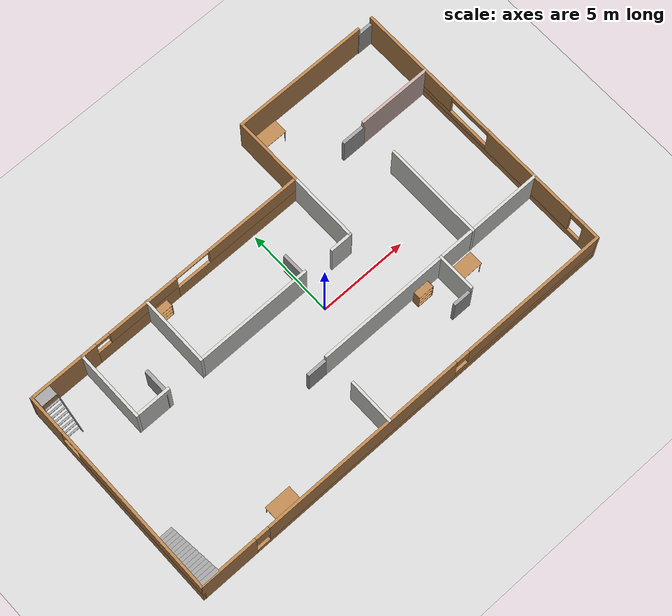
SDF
<sdf version="1.6">
 <world name="default">
  <light name="sun" type="directional">
   <pose>0 0 10 0 -0 0</pose>
   <diffuse>0.8 0.8 0.8 1</diffuse>
   <specular>0.2 0.2 0.2 1</specular>
   <attenuation>
    <range>1000</range>
    <constant>0.9</constant>
    <linear>0.01</linear>
    <quadratic>0.001</quadratic>
   </attenuation>
   <direction>-0.5 0.1 -0.9</direction>
   <spot><inner_angle>0</inner_angle><outer_angle>0</outer_angle><falloff>0</falloff></spot>
  </light>
  <model name="ground_plane">
   <static>1</static>
   <link name="link">
    <collision name="collision">
     <geometry><plane><normal>0 0 1</normal><size>100 100</size></plane></geometry>
     <surface>
      <contact><collide_bitmask>65535</collide_bitmask></contact>
      <friction><ode><mu>100</mu><mu2>50</mu2></ode></friction>
     </surface>
    </collision>
    <visual name="visual">
     <cast_shadows>0</cast_shadows>
     <geometry><plane><normal>0 0 1</normal><size>100 100</size></plane></geometry>
     <material>
      <script><uri>file://media/materials/scripts/gazebo.material</uri><name>Gazebo/Grey</name></script>
     </material>
    </visual>
   </link>
  </model>
  <gravity>0 0 -9.8</gravity>
  <magnetic_field>6e-06 2.3e-05 -4.2e-05</magnetic_field>
  <atmosphere type="adiabatic"/>
  <physics name="default_physics" default="0" type="ode">
   <max_step_size>0.001</max_step_size>
   <real_time_factor>1</real_time_factor>
   <real_time_update_rate>1000</real_time_update_rate>
  </physics>
  <scene><ambient>0.4 0.4 0.4 1</ambient><background>0.7 0.7 0.7 1</background><shadows>1</shadows></scene>
  <spherical_coordinates>
   <surface_model>EARTH_WGS84</surface_model>
   <latitude_deg>0</latitude_deg>
   <longitude_deg>0</longitude_deg>
   <elevation>0</elevation>
   <heading_deg>0</heading_deg>
  </spherical_coordinates>
  <model name="table">
   <static>1</static>
   <link name="link">
    <collision name="surface">
     <pose>0 0 1 0 -0 0</pose>
     <geometry><box><size>1.5 0.8 0.03</size></box></geometry>
     <surface><friction><ode><mu>0.6</mu><mu2>0.6</mu2></ode></friction></surface>
    </collision>
    <visual name="visual1">
     <pose>0 0 1 0 -0 0</pose>
     <geometry><box><size>1.5 0.8 0.03</size></box></geometry>
     <material>
      <script><uri>file://media/materials/scripts/gazebo.material</uri><name>Gazebo/Wood</name></script>
     </material>
    </visual>
    <collision name="front_left_leg">
     <pose>0.68 0.38 0.5 0 -0 0</pose>
     <geometry><cylinder><radius>0.02</radius><length>1</length></cylinder></geometry>
    </collision>
    <visual name="front_left_leg">
     <pose>0.68 0.38 0.5 0 -0 0</pose>
     <geometry><cylinder><radius>0.02</radius><length>1</length></cylinder></geometry>
     <material>
      <script><uri>file://media/materials/scripts/gazebo.material</uri><name>Gazebo/Grey</name></script>
     </material>
    </visual>
    <collision name="front_right_leg">
     <pose>0.68 -0.38 0.5 0 -0 0</pose>
     <geometry><cylinder><radius>0.02</radius><length>1</length></cylinder></geometry>
    </collision>
    <visual name="front_right_leg">
     <pose>0.68 -0.38 0.5 0 -0 0</pose>
     <geometry><cylinder><radius>0.02</radius><length>1</length></cylinder></geometry>
     <material>
      <script><uri>file://media/materials/scripts/gazebo.material</uri><name>Gazebo/Grey</name></script>
     </material>
    </visual>
    <collision name="back_right_leg">
     <pose>-0.68 -0.38 0.5 0 -0 0</pose>
     <geometry><cylinder><radius>0.02</radius><length>1</length></cylinder></geometry>
    </collision>
    <visual name="back_right_leg">
     <pose>-0.68 -0.38 0.5 0 -0 0</pose>
     <geometry><cylinder><radius>0.02</radius><length>1</length></cylinder></geometry>
     <material>
      <script><uri>file://media/materials/scripts/gazebo.material</uri><name>Gazebo/Grey</name></script>
     </material>
    </visual>
    <collision name="back_left_leg">
     <pose>-0.68 0.38 0.5 0 -0 0</pose>
     <geometry><cylinder><radius>0.02</radius><length>1</length></cylinder></geometry>
    </collision>
    <visual name="back_left_leg">
     <pose>-0.68 0.38 0.5 0 -0 0</pose>
     <geometry><cylinder><radius>0.02</radius><length>1</length></cylinder></geometry>
     <material>
      <script><uri>file://media/materials/scripts/gazebo.material</uri><name>Gazebo/Grey</name></script>
     </material>
    </visual>
   </link>
   <pose>3.83374 8.23259 0 0 -0 0</pose>
  </model>
  <model name="bookshelf">
   <static>1</static>
   <link name="link">
    <inertial><mass>1</mass></inertial>
    <collision name="back">
     <pose>0 0.005 0.6 0 -0 0</pose>
     <geometry><box><size>0.9 0.01 1.2</size></box></geometry>
    </collision>
    <visual name="visual1">
     <pose>0 0.005 0.6 0 -0 0</pose>
     <geometry><box><size>0.9 0.01 1.2</size></box></geometry>
     <material>
      <script><uri>file://media/materials/scripts/gazebo.material</uri><name>Gazebo/Wood</name></script>
     </material>
    </visual>
    <collision name="left_side">
     <pose>0.45 -0.195 0.6 0 -0 0</pose>
     <geometry><box><size>0.02 0.4 1.2</size></box></geometry>
    </collision>
    <visual name="visual2">
     <pose>0.45 -0.195 0.6 0 -0 0</pose>
     <geometry><box><size>0.02 0.4 1.2</size></box></geometry>
     <material>
      <script><uri>file://media/materials/scripts/gazebo.material</uri><name>Gazebo/Wood</name></script>
     </material>
    </visual>
    <collision name="right_side">
     <pose>-0.45 -0.195 0.6 0 -0 0</pose>
     <geometry><box><size>0.02 0.4 1.2</size></box></geometry>
    </collision>
    <visual name="visual3">
     <pose>-0.45 -0.195 0.6 0 -0 0</pose>
     <geometry><box><size>0.02 0.4 1.2</size></box></geometry>
     <material>
      <script><uri>file://media/materials/scripts/gazebo.material</uri><name>Gazebo/Wood</name></script>
     </material>
    </visual>
    <collision name="bottom">
     <pose>0 -0.195 0.03 0 -0 0</pose>
     <geometry><box><size>0.88 0.4 0.06</size></box></geometry>
    </collision>
    <visual name="visual4">
     <pose>0 -0.195 0.03 0 -0 0</pose>
     <geometry><box><size>0.88 0.4 0.06</size></box></geometry>
     <material>
      <script><uri>file://media/materials/scripts/gazebo.material</uri><name>Gazebo/Wood</name></script>
     </material>
    </visual>
    <collision name="top">
     <pose>0 -0.195 1.19 0 -0 0</pose>
     <geometry><box><size>0.88 0.4 0.02</size></box></geometry>
    </collision>
    <visual name="visual5">
     <pose>0 -0.195 1.19 0 -0 0</pose>
     <geometry><box><size>0.88 0.4 0.02</size></box></geometry>
     <material>
      <script><uri>file://media/materials/scripts/gazebo.material</uri><name>Gazebo/Wood</name></script>
     </material>
    </visual>
    <collision name="low_shelf">
     <pose>0 -0.195 0.43 0 -0 0</pose>
     <geometry><box><size>0.88 0.4 0.02</size></box></geometry>
    </collision>
    <visual name="visual6">
     <pose>0 -0.195 0.43 0 -0 0</pose>
     <geometry><box><size>0.88 0.4 0.02</size></box></geometry>
     <material>
      <script><uri>file://media/materials/scripts/gazebo.material</uri><name>Gazebo/Wood</name></script>
     </material>
    </visual>
    <collision name="high_shelf">
     <pose>0 -0.195 0.8 0 -0 0</pose>
     <geometry><box><size>0.88 0.4 0.02</size></box></geometry>
    </collision>
    <visual name="visual7">
     <pose>0 -0.195 0.8 0 -0 0</pose>
     <geometry><box><size>0.88 0.4 0.02</size></box></geometry>
     <material>
      <script><uri>file://media/materials/scripts/gazebo.material</uri><name>Gazebo/Wood</name></script>
     </material>
    </visual>
   </link>
   <pose>-5.94941 5.06347 0 0 -0 0</pose>
  </model>
  <model name="ladder_60deg_0rails">
   <static>1</static>
   <link name="step0">
    <pose>0 0.15396 0.266667 0 -0 0</pose>
    <inertial>
     <mass>9.75482</mass>
     <inertia>
      <ixx>0.00957124</ixx>
      <iyy>0.65963</iyy>
      <izz>0.666842</izz>
      <ixy>0</ixy>
      <ixz>0</ixz>
      <iyz>0</iyz>
     </inertia>
    </inertial>
    <collision name="collision"><geometry><box><size>0.9 0.1016 0.0381</size></box></geometry></collision>
    <visual name="visual">
     <geometry><box><size>0.9 0.1016 0.0381</size></box></geometry>
     <material>
      <script><uri>file://media/materials/scripts/gazebo.material</uri><name>Gazebo/Grey</name></script>
     </material>
    </visual>
   </link>
   <link name="step1">
    <pose>0 0.30792 0.533333 0 -0 0</pose>
    <inertial>
     <mass>9.75482</mass>
     <inertia>
      <ixx>0.00957124</ixx>
      <iyy>0.65963</iyy>
      <izz>0.666842</izz>
      <ixy>0</ixy>
      <ixz>0</ixz>
      <iyz>0</iyz>
     </inertia>
    </inertial>
    <collision name="collision"><geometry><box><size>0.9 0.1016 0.0381</size></box></geometry></collision>
    <visual name="visual">
     <geometry><box><size>0.9 0.1016 0.0381</size></box></geometry>
     <material>
      <script><uri>file://media/materials/scripts/gazebo.material</uri><name>Gazebo/Grey</name></script>
     </material>
    </visual>
   </link>
   <link name="step2">
    <pose>0 0.46188 0.8 0 -0 0</pose>
    <inertial>
     <mass>9.75482</mass>
     <inertia>
      <ixx>0.00957124</ixx>
      <iyy>0.65963</iyy>
      <izz>0.666842</izz>
      <ixy>0</ixy>
      <ixz>0</ixz>
      <iyz>0</iyz>
     </inertia>
    </inertial>
    <collision name="collision"><geometry><box><size>0.9 0.1016 0.0381</size></box></geometry></collision>
    <visual name="visual">
     <geometry><box><size>0.9 0.1016 0.0381</size></box></geometry>
     <material>
      <script><uri>file://media/materials/scripts/gazebo.material</uri><name>Gazebo/Grey</name></script>
     </material>
    </visual>
   </link>
   <link name="step3">
    <pose>0 0.61584 1.06667 0 -0 0</pose>
    <inertial>
     <mass>9.75482</mass>
     <inertia>
      <ixx>0.00957124</ixx>
      <iyy>0.65963</iyy>
      <izz>0.666842</izz>
      <ixy>0</ixy>
      <ixz>0</ixz>
      <iyz>0</iyz>
     </inertia>
    </inertial>
    <collision name="collision"><geometry><box><size>0.9 0.1016 0.0381</size></box></geometry></collision>
    <visual name="visual">
     <geometry><box><size>0.9 0.1016 0.0381</size></box></geometry>
     <material>
      <script><uri>file://media/materials/scripts/gazebo.material</uri><name>Gazebo/Grey</name></script>
     </material>
    </visual>
   </link>
   <link name="step4">
    <pose>0 0.7698 1.33333 0 -0 0</pose>
    <inertial>
     <mass>9.75482</mass>
     <inertia>
      <ixx>0.00957124</ixx>
      <iyy>0.65963</iyy>
      <izz>0.666842</izz>
      <ixy>0</ixy>
      <ixz>0</ixz>
      <iyz>0</iyz>
     </inertia>
    </inertial>
    <collision name="collision"><geometry><box><size>0.9 0.1016 0.0381</size></box></geometry></collision>
    <visual name="visual">
     <geometry><box><size>0.9 0.1016 0.0381</size></box></geometry>
     <material>
      <script><uri>file://media/materials/scripts/gazebo.material</uri><name>Gazebo/Grey</name></script>
     </material>
    </visual>
   </link>
   <link name="step5">
    <pose>0 0.92376 1.6 0 -0 0</pose>
    <inertial>
     <mass>9.75482</mass>
     <inertia>
      <ixx>0.00957124</ixx>
      <iyy>0.65963</iyy>
      <izz>0.666842</izz>
      <ixy>0</ixy>
      <ixz>0</ixz>
      <iyz>0</iyz>
     </inertia>
    </inertial>
    <collision name="collision"><geometry><box><size>0.9 0.1016 0.0381</size></box></geometry></collision>
    <visual name="visual">
     <geometry><box><size>0.9 0.1016 0.0381</size></box></geometry>
     <material>
      <script><uri>file://media/materials/scripts/gazebo.material</uri><name>Gazebo/Grey</name></script>
     </material>
    </visual>
   </link>
   <link name="step6">
    <pose>0 1.07772 1.86667 0 -0 0</pose>
    <inertial>
     <mass>9.75482</mass>
     <inertia>
      <ixx>0.00957124</ixx>
      <iyy>0.65963</iyy>
      <izz>0.666842</izz>
      <ixy>0</ixy>
      <ixz>0</ixz>
      <iyz>0</iyz>
     </inertia>
    </inertial>
    <collision name="collision"><geometry><box><size>0.9 0.1016 0.0381</size></box></geometry></collision>
    <visual name="visual">
     <geometry><box><size>0.9 0.1016 0.0381</size></box></geometry>
     <material>
      <script><uri>file://media/materials/scripts/gazebo.material</uri><name>Gazebo/Grey</name></script>
     </material>
    </visual>
   </link>
   <link name="step7">
    <pose>0 1.23168 2.13333 0 -0 0</pose>
    <inertial>
     <mass>9.75482</mass>
     <inertia>
      <ixx>0.00957124</ixx>
      <iyy>0.65963</iyy>
      <izz>0.666842</izz>
      <ixy>0</ixy>
      <ixz>0</ixz>
      <iyz>0</iyz>
     </inertia>
    </inertial>
    <collision name="collision"><geometry><box><size>0.9 0.1016 0.0381</size></box></geometry></collision>
    <visual name="visual">
     <geometry><box><size>0.9 0.1016 0.0381</size></box></geometry>
     <material>
      <script><uri>file://media/materials/scripts/gazebo.material</uri><name>Gazebo/Grey</name></script>
     </material>
    </visual>
   </link>
   <link name="landing">
    <pose>0 1.68564 2.4 0 -0 0</pose>
    <inertial>
     <mass>57.6072</mass>
     <inertia><ixx>1.73518</ixx><iyy>3.89545</iyy><izz>5.6167</izz><ixy>0</ixy><ixz>0</ixz><iyz>0</iyz></inertia>
    </inertial>
    <collision name="collision"><geometry><box><size>0.9 0.6 0.1016</size></box></geometry></collision>
    <visual name="visual">
     <geometry><box><size>0.9 0.6 0.1016</size></box></geometry>
     <material>
      <script><uri>file://media/materials/scripts/gazebo.material</uri><name>Gazebo/Grey</name></script>
     </material>
    </visual>
   </link>
   <link name="left_side_wall">
    <pose>-0.45 0.69282 1.2 1.0472 -0 0</pose>
    <collision name="collision"><geometry><box><size>0.0508 2.85128 0.13</size></box></geometry></collision>
    <visual name="visual">
     <geometry><box><size>0.0508 2.85128 0.13</size></box></geometry>
     <material>
      <script><uri>file://media/materials/scripts/gazebo.material</uri><name>Gazebo/Grey</name></script>
     </material>
    </visual>
   </link>
   <link name="right_side_wall">
    <pose>0.45 0.69282 1.2 1.0472 -0 0</pose>
    <collision name="collision"><geometry><box><size>0.0508 2.85128 0.13</size></box></geometry></collision>
    <visual name="visual">
     <geometry><box><size>0.0508 2.85128 0.13</size></box></geometry>
     <material>
      <script><uri>file://media/materials/scripts/gazebo.material</uri><name>Gazebo/Grey</name></script>
     </material>
    </visual>
   </link>
   <pose>-12.9394 3.18019 0 0 -0 0</pose>
  </model>
  <model name="wooden_peg">
   <link name="link">
    <pose>0 0 0.04 0 -0 0</pose>
    <inertial>
     <mass>0.0175</mass>
     <inertia>
      <ixx>9.74923e-06</ixx>
      <ixy>0</ixy>
      <ixz>0</ixz>
      <iyy>9.74923e-06</iyy>
      <iyz>0</iyz>
      <izz>8.31797e-07</izz>
     </inertia>
    </inertial>
    <collision name="collision">
     <geometry><cylinder><radius>0.00975</radius><length>0.08</length></cylinder></geometry>
     <surface>
      <contact>
       <poissons_ratio>0.347</poissons_ratio>
       <elastic_modulus>8.8e+09</elastic_modulus>
       <ode><kp>100000</kp><kd>100</kd><max_vel>100</max_vel><min_depth>0.001</min_depth></ode>
      </contact>
      <friction>
       <torsional>
        <coefficient>1</coefficient>
        <use_patch_radius>0</use_patch_radius>
        <surface_radius>0.01</surface_radius>
       </torsional>
      </friction>
     </surface>
    </collision>
    <visual name="visual">
     <geometry><cylinder><radius>0.00975</radius><length>0.08</length></cylinder></geometry>
     <material>
      <script><uri>file://media/materials/scripts/gazebo.material</uri><name>Gazebo/Wood</name></script>
     </material>
    </visual>
   </link>
   <pose>-12.4611 3.34456 0.008749 1.5708 0.065584 -0.003718</pose>
  </model>
  <model name="table_0">
   <static>1</static>
   <link name="link">
    <collision name="surface">
     <pose>0 0 1 0 -0 0</pose>
     <geometry><box><size>1.5 0.8 0.03</size></box></geometry>
     <surface><friction><ode><mu>0.6</mu><mu2>0.6</mu2></ode></friction></surface>
    </collision>
    <visual name="visual1">
     <pose>0 0 1 0 -0 0</pose>
     <geometry><box><size>1.5 0.8 0.03</size></box></geometry>
     <material>
      <script><uri>file://media/materials/scripts/gazebo.material</uri><name>Gazebo/Wood</name></script>
     </material>
    </visual>
    <collision name="front_left_leg">
     <pose>0.68 0.38 0.5 0 -0 0</pose>
     <geometry><cylinder><radius>0.02</radius><length>1</length></cylinder></geometry>
    </collision>
    <visual name="front_left_leg">
     <pose>0.68 0.38 0.5 0 -0 0</pose>
     <geometry><cylinder><radius>0.02</radius><length>1</length></cylinder></geometry>
     <material>
      <script><uri>file://media/materials/scripts/gazebo.material</uri><name>Gazebo/Grey</name></script>
     </material>
    </visual>
    <collision name="front_right_leg">
     <pose>0.68 -0.38 0.5 0 -0 0</pose>
     <geometry><cylinder><radius>0.02</radius><length>1</length></cylinder></geometry>
    </collision>
    <visual name="front_right_leg">
     <pose>0.68 -0.38 0.5 0 -0 0</pose>
     <geometry><cylinder><radius>0.02</radius><length>1</length></cylinder></geometry>
     <material>
      <script><uri>file://media/materials/scripts/gazebo.material</uri><name>Gazebo/Grey</name></script>
     </material>
    </visual>
    <collision name="back_right_leg">
     <pose>-0.68 -0.38 0.5 0 -0 0</pose>
     <geometry><cylinder><radius>0.02</radius><length>1</length></cylinder></geometry>
    </collision>
    <visual name="back_right_leg">
     <pose>-0.68 -0.38 0.5 0 -0 0</pose>
     <geometry><cylinder><radius>0.02</radius><length>1</length></cylinder></geometry>
     <material>
      <script><uri>file://media/materials/scripts/gazebo.material</uri><name>Gazebo/Grey</name></script>
     </material>
    </visual>
    <collision name="back_left_leg">
     <pose>-0.68 0.38 0.5 0 -0 0</pose>
     <geometry><cylinder><radius>0.02</radius><length>1</length></cylinder></geometry>
    </collision>
    <visual name="back_left_leg">
     <pose>-0.68 0.38 0.5 0 -0 0</pose>
     <geometry><cylinder><radius>0.02</radius><length>1</length></cylinder></geometry>
     <material>
      <script><uri>file://media/materials/scripts/gazebo.material</uri><name>Gazebo/Grey</name></script>
     </material>
    </visual>
   </link>
   <pose>-8.01928 -5.95607 0 0 -0 0</pose>
  </model>
  <model name="table_1">
   <static>1</static>
   <link name="link">
    <collision name="surface">
     <pose>0 0 1 0 -0 0</pose>
     <geometry><box><size>1.5 0.8 0.03</size></box></geometry>
     <surface><friction><ode><mu>0.6</mu><mu2>0.6</mu2></ode></friction></surface>
    </collision>
    <visual name="visual1">
     <pose>0 0 1 0 -0 0</pose>
     <geometry><box><size>1.5 0.8 0.03</size></box></geometry>
     <material>
      <script><uri>file://media/materials/scripts/gazebo.material</uri><name>Gazebo/Wood</name></script>
     </material>
    </visual>
    <collision name="front_left_leg">
     <pose>0.68 0.38 0.5 0 -0 0</pose>
     <geometry><cylinder><radius>0.02</radius><length>1</length></cylinder></geometry>
    </collision>
    <visual name="front_left_leg">
     <pose>0.68 0.38 0.5 0 -0 0</pose>
     <geometry><cylinder><radius>0.02</radius><length>1</length></cylinder></geometry>
     <material>
      <script><uri>file://media/materials/scripts/gazebo.material</uri><name>Gazebo/Grey</name></script>
     </material>
    </visual>
    <collision name="front_right_leg">
     <pose>0.68 -0.38 0.5 0 -0 0</pose>
     <geometry><cylinder><radius>0.02</radius><length>1</length></cylinder></geometry>
    </collision>
    <visual name="front_right_leg">
     <pose>0.68 -0.38 0.5 0 -0 0</pose>
     <geometry><cylinder><radius>0.02</radius><length>1</length></cylinder></geometry>
     <material>
      <script><uri>file://media/materials/scripts/gazebo.material</uri><name>Gazebo/Grey</name></script>
     </material>
    </visual>
    <collision name="back_right_leg">
     <pose>-0.68 -0.38 0.5 0 -0 0</pose>
     <geometry><cylinder><radius>0.02</radius><length>1</length></cylinder></geometry>
    </collision>
    <visual name="back_right_leg">
     <pose>-0.68 -0.38 0.5 0 -0 0</pose>
     <geometry><cylinder><radius>0.02</radius><length>1</length></cylinder></geometry>
     <material>
      <script><uri>file://media/materials/scripts/gazebo.material</uri><name>Gazebo/Grey</name></script>
     </material>
    </visual>
    <collision name="back_left_leg">
     <pose>-0.68 0.38 0.5 0 -0 0</pose>
     <geometry><cylinder><radius>0.02</radius><length>1</length></cylinder></geometry>
    </collision>
    <visual name="back_left_leg">
     <pose>-0.68 0.38 0.5 0 -0 0</pose>
     <geometry><cylinder><radius>0.02</radius><length>1</length></cylinder></geometry>
     <material>
      <script><uri>file://media/materials/scripts/gazebo.material</uri><name>Gazebo/Grey</name></script>
     </material>
    </visual>
   </link>
   <pose>6.12704 -3.2004 0 0 -0 0</pose>
  </model>
  <model name="bookshelf_0">
   <static>1</static>
   <link name="link">
    <inertial><mass>1</mass></inertial>
    <collision name="back">
     <pose>0 0.005 0.6 0 -0 0</pose>
     <geometry><box><size>0.9 0.01 1.2</size></box></geometry>
    </collision>
    <visual name="visual1">
     <pose>0 0.005 0.6 0 -0 0</pose>
     <geometry><box><size>0.9 0.01 1.2</size></box></geometry>
     <material>
      <script><uri>file://media/materials/scripts/gazebo.material</uri><name>Gazebo/Wood</name></script>
     </material>
    </visual>
    <collision name="left_side">
     <pose>0.45 -0.195 0.6 0 -0 0</pose>
     <geometry><box><size>0.02 0.4 1.2</size></box></geometry>
    </collision>
    <visual name="visual2">
     <pose>0.45 -0.195 0.6 0 -0 0</pose>
     <geometry><box><size>0.02 0.4 1.2</size></box></geometry>
     <material>
      <script><uri>file://media/materials/scripts/gazebo.material</uri><name>Gazebo/Wood</name></script>
     </material>
    </visual>
    <collision name="right_side">
     <pose>-0.45 -0.195 0.6 0 -0 0</pose>
     <geometry><box><size>0.02 0.4 1.2</size></box></geometry>
    </collision>
    <visual name="visual3">
     <pose>-0.45 -0.195 0.6 0 -0 0</pose>
     <geometry><box><size>0.02 0.4 1.2</size></box></geometry>
     <material>
      <script><uri>file://media/materials/scripts/gazebo.material</uri><name>Gazebo/Wood</name></script>
     </material>
    </visual>
    <collision name="bottom">
     <pose>0 -0.195 0.03 0 -0 0</pose>
     <geometry><box><size>0.88 0.4 0.06</size></box></geometry>
    </collision>
    <visual name="visual4">
     <pose>0 -0.195 0.03 0 -0 0</pose>
     <geometry><box><size>0.88 0.4 0.06</size></box></geometry>
     <material>
      <script><uri>file://media/materials/scripts/gazebo.material</uri><name>Gazebo/Wood</name></script>
     </material>
    </visual>
    <collision name="top">
     <pose>0 -0.195 1.19 0 -0 0</pose>
     <geometry><box><size>0.88 0.4 0.02</size></box></geometry>
    </collision>
    <visual name="visual5">
     <pose>0 -0.195 1.19 0 -0 0</pose>
     <geometry><box><size>0.88 0.4 0.02</size></box></geometry>
     <material>
      <script><uri>file://media/materials/scripts/gazebo.material</uri><name>Gazebo/Wood</name></script>
     </material>
    </visual>
    <collision name="low_shelf">
     <pose>0 -0.195 0.43 0 -0 0</pose>
     <geometry><box><size>0.88 0.4 0.02</size></box></geometry>
    </collision>
    <visual name="visual6">
     <pose>0 -0.195 0.43 0 -0 0</pose>
     <geometry><box><size>0.88 0.4 0.02</size></box></geometry>
     <material>
      <script><uri>file://media/materials/scripts/gazebo.material</uri><name>Gazebo/Wood</name></script>
     </material>
    </visual>
    <collision name="high_shelf">
     <pose>0 -0.195 0.8 0 -0 0</pose>
     <geometry><box><size>0.88 0.4 0.02</size></box></geometry>
    </collision>
    <visual name="visual7">
     <pose>0 -0.195 0.8 0 -0 0</pose>
     <geometry><box><size>0.88 0.4 0.02</size></box></geometry>
     <material>
      <script><uri>file://media/materials/scripts/gazebo.material</uri><name>Gazebo/Wood</name></script>
     </material>
    </visual>
   </link>
   <pose>3.85647 -2.55218 0 0 -0 0</pose>
  </model>
  <model name="ball_bearing">
   <link name="link">
    <pose>0 0 0.003 0 -0 0</pose>
    <inertial>
     <mass>0.0011</mass>
     <inertia>
      <ixx>3.96e-09</ixx>
      <ixy>0</ixy>
      <ixz>0</ixz>
      <iyy>3.96e-09</iyy>
      <iyz>0</iyz>
      <izz>3.96e-09</izz>
     </inertia>
    </inertial>
    <collision name="collision">
     <geometry><sphere><radius>0.003</radius></sphere></geometry>
     <surface>
      <contact>
       <poissons_ratio>0.305</poissons_ratio>
       <elastic_modulus>2e+11</elastic_modulus>
       <ode><kp>100000</kp><kd>100</kd><max_vel>100</max_vel><min_depth>0.001</min_depth></ode>
      </contact>
      <friction>
       <torsional>
        <coefficient>1</coefficient>
        <use_patch_radius>0</use_patch_radius>
        <surface_radius>0.01</surface_radius>
       </torsional>
      </friction>
     </surface>
    </collision>
    <visual name="visual">
     <geometry><sphere><radius>0.003</radius></sphere></geometry>
     <material>
      <script><uri>file://media/materials/scripts/gazebo.material</uri><name>Gazebo/Grey</name></script>
     </material>
    </visual>
    <velocity_decay><linear>0</linear><angular>0.005</angular></velocity_decay>
   </link>
   <pose>-4.0826 -9.05693 -0.000558 0 -0 0</pose>
  </model>
  <model name="MyHouse">
   <link name="Door_0">
    <pose>-7.57412 0.838443 0 0 -0 1.57987</pose>
    <inertial>
     <inertia><ixx>0</ixx><ixy>0</ixy><ixz>0</ixz><iyy>0</iyy><iyz>0</iyz><izz>0</izz></inertia>
     <mass>0</mass>
    </inertial>
    <visual name="Door_0_Visual">
     <pose>0 0 1 0 -0 0</pose>
     <geometry><box><size>1.56098 0.2 2</size></box></geometry>
     <material>
      <script><uri>file://media/materials/scripts/gazebo.material</uri><name>Gazebo/Grey</name></script>
      <shader type="pixel"/>
     </material>
    </visual>
    <collision name="Door_0_Collision">
     <pose>0 0 1 0 -0 0</pose>
     <geometry><box><size>1.56098 0.2 2</size></box></geometry>
     <surface>
      <friction>
       <ode><mu>1</mu><mu2>1</mu2><fdir1>0 0 0</fdir1><slip1>0</slip1><slip2>0</slip2></ode>
       <torsional>
        <coefficient>1</coefficient>
        <patch_radius>0</patch_radius>
        <surface_radius>0</surface_radius>
        <use_patch_radius>1</use_patch_radius>
        <ode><slip>0</slip></ode>
       </torsional>
      </friction>
      <bounce><restitution_coefficient>0</restitution_coefficient><threshold>1e+06</threshold></bounce>
      <contact>
       <collide_without_contact>0</collide_without_contact>
       <collide_without_contact_bitmask>1</collide_without_contact_bitmask>
       <collide_bitmask>1</collide_bitmask>
       <ode>
        <soft_cfm>0</soft_cfm>
        <soft_erp>0.2</soft_erp>
        <kp>1e+13</kp>
        <kd>1</kd>
        <max_vel>0.01</max_vel>
        <min_depth>0</min_depth>
       </ode>
       <bullet>
        <split_impulse>1</split_impulse>
        <split_impulse_penetration_threshold>-0.01</split_impulse_penetration_threshold>
        <soft_cfm>0</soft_cfm>
        <soft_erp>0.2</soft_erp>
        <kp>1e+13</kp>
        <kd>1</kd>
       </bullet>
      </contact>
     </surface>
    </collision>
   </link>
   <link name="Door_2">
    <pose>11.9351 7.82689 0 0 -0 0</pose>
    <visual name="Door_2_Visual">
     <pose>0 0 1 0 -0 0</pose>
     <geometry><box><size>0.9 0.17 2</size></box></geometry>
     <material>
      <script><uri>file://media/materials/scripts/gazebo.material</uri><name>Gazebo/Grey</name></script>
      <shader type="pixel"/>
     </material>
    </visual>
    <collision name="Door_2_Collision">
     <pose>0 0 1 0 -0 0</pose>
     <geometry><box><size>0.9 0.17 2</size></box></geometry>
     <surface>
      <friction>
       <ode><mu>1</mu><mu2>1</mu2><fdir1>0 0 0</fdir1><slip1>0</slip1><slip2>0</slip2></ode>
       <torsional>
        <coefficient>1</coefficient>
        <patch_radius>0</patch_radius>
        <surface_radius>0</surface_radius>
        <use_patch_radius>1</use_patch_radius>
        <ode><slip>0</slip></ode>
       </torsional>
      </friction>
      <bounce><restitution_coefficient>0</restitution_coefficient><threshold>1e+06</threshold></bounce>
      <contact>
       <collide_without_contact>0</collide_without_contact>
       <collide_without_contact_bitmask>1</collide_without_contact_bitmask>
       <collide_bitmask>1</collide_bitmask>
       <ode>
        <soft_cfm>0</soft_cfm>
        <soft_erp>0.2</soft_erp>
        <kp>1e+13</kp>
        <kd>1</kd>
        <max_vel>0.01</max_vel>
        <min_depth>0</min_depth>
       </ode>
       <bullet>
        <split_impulse>1</split_impulse>
        <split_impulse_penetration_threshold>-0.01</split_impulse_penetration_threshold>
        <soft_cfm>0</soft_cfm>
        <soft_erp>0.2</soft_erp>
        <kp>1e+13</kp>
        <kd>1</kd>
       </bullet>
      </contact>
     </surface>
    </collision>
   </link>
   <link name="Door_3">
    <pose>1.0088 0.841968 0 0 -0 1.57718</pose>
    <inertial>
     <inertia><ixx>0</ixx><ixy>0</ixy><ixz>0</ixz><iyy>0</iyy><iyz>0</iyz><izz>0</izz></inertia>
     <mass>0</mass>
    </inertial>
    <visual name="Door_3_Visual">
     <pose>0 0 1 0 -0 0</pose>
     <geometry><box><size>1.47298 0.17 2</size></box></geometry>
     <material>
      <script><uri>file://media/materials/scripts/gazebo.material</uri><name>Gazebo/Grey</name></script>
      <shader type="pixel"/>
     </material>
    </visual>
    <collision name="Door_3_Collision">
     <pose>0 0 1 0 -0 0</pose>
     <geometry><box><size>1.47298 0.17 2</size></box></geometry>
     <surface>
      <friction>
       <ode><mu>1</mu><mu2>1</mu2><fdir1>0 0 0</fdir1><slip1>0</slip1><slip2>0</slip2></ode>
       <torsional>
        <coefficient>1</coefficient>
        <patch_radius>0</patch_radius>
        <surface_radius>0</surface_radius>
        <use_patch_radius>1</use_patch_radius>
        <ode><slip>0</slip></ode>
       </torsional>
      </friction>
      <bounce><restitution_coefficient>0</restitution_coefficient><threshold>1e+06</threshold></bounce>
      <contact>
       <collide_without_contact>0</collide_without_contact>
       <collide_without_contact_bitmask>1</collide_without_contact_bitmask>
       <collide_bitmask>1</collide_bitmask>
       <ode>
        <soft_cfm>0</soft_cfm>
        <soft_erp>0.2</soft_erp>
        <kp>1e+13</kp>
        <kd>1</kd>
        <max_vel>0.01</max_vel>
        <min_depth>0</min_depth>
       </ode>
       <bullet>
        <split_impulse>1</split_impulse>
        <split_impulse_penetration_threshold>-0.01</split_impulse_penetration_threshold>
        <soft_cfm>0</soft_cfm>
        <soft_erp>0.2</soft_erp>
        <kp>1e+13</kp>
        <kd>1</kd>
       </bullet>
      </contact>
     </surface>
    </collision>
   </link>
   <link name="Door_4">
    <pose>7.66176 3.99526 0 0 -0 0</pose>
    <inertial>
     <inertia><ixx>0</ixx><ixy>0</ixy><ixz>0</ixz><iyy>0</iyy><iyz>0</iyz><izz>0</izz></inertia>
     <mass>0</mass>
    </inertial>
    <visual name="Door_4_Visual">
     <pose>0 0 1 0 -0 0</pose>
     <geometry><box><size>1.33624 0.17 2</size></box></geometry>
     <material>
      <script><uri>file://media/materials/scripts/gazebo.material</uri><name>Gazebo/Grey</name></script>
      <shader type="pixel"/>
     </material>
    </visual>
    <collision name="Door_4_Collision">
     <pose>0 0 1 0 -0 0</pose>
     <geometry><box><size>1.33624 0.17 2</size></box></geometry>
     <surface>
      <friction>
       <ode><mu>1</mu><mu2>1</mu2><fdir1>0 0 0</fdir1><slip1>0</slip1><slip2>0</slip2></ode>
       <torsional>
        <coefficient>1</coefficient>
        <patch_radius>0</patch_radius>
        <surface_radius>0</surface_radius>
        <use_patch_radius>1</use_patch_radius>
        <ode><slip>0</slip></ode>
       </torsional>
      </friction>
      <bounce><restitution_coefficient>0</restitution_coefficient><threshold>1e+06</threshold></bounce>
      <contact>
       <collide_without_contact>0</collide_without_contact>
       <collide_without_contact_bitmask>1</collide_without_contact_bitmask>
       <collide_bitmask>1</collide_bitmask>
       <ode>
        <soft_cfm>0</soft_cfm>
        <soft_erp>0.2</soft_erp>
        <kp>1e+13</kp>
        <kd>1</kd>
        <max_vel>0.01</max_vel>
        <min_depth>0</min_depth>
       </ode>
       <bullet>
        <split_impulse>1</split_impulse>
        <split_impulse_penetration_threshold>-0.01</split_impulse_penetration_threshold>
        <soft_cfm>0</soft_cfm>
        <soft_erp>0.2</soft_erp>
        <kp>1e+13</kp>
        <kd>1</kd>
       </bullet>
      </contact>
     </surface>
    </collision>
   </link>
   <link name="Door_6">
    <pose>-1.63334 -3.5898 0 0 -0 0</pose>
    <inertial>
     <inertia><ixx>0</ixx><ixy>0</ixy><ixz>0</ixz><iyy>0</iyy><iyz>0</iyz><izz>0</izz></inertia>
     <mass>0</mass>
    </inertial>
    <visual name="Door_6_Visual">
     <pose>0 0 1 0 -0 0</pose>
     <geometry><box><size>1.13121 0.17 2</size></box></geometry>
     <material>
      <script><uri>file://media/materials/scripts/gazebo.material</uri><name>Gazebo/Grey</name></script>
      <shader type="pixel"/>
     </material>
    </visual>
    <collision name="Door_6_Collision">
     <pose>0 0 1 0 -0 0</pose>
     <geometry><box><size>1.13121 0.17 2</size></box></geometry>
     <surface>
      <friction>
       <ode><mu>1</mu><mu2>1</mu2><fdir1>0 0 0</fdir1><slip1>0</slip1><slip2>0</slip2></ode>
       <torsional>
        <coefficient>1</coefficient>
        <patch_radius>0</patch_radius>
        <surface_radius>0</surface_radius>
        <use_patch_radius>1</use_patch_radius>
        <ode><slip>0</slip></ode>
       </torsional>
      </friction>
      <bounce><restitution_coefficient>0</restitution_coefficient><threshold>1e+06</threshold></bounce>
      <contact>
       <collide_without_contact>0</collide_without_contact>
       <collide_without_contact_bitmask>1</collide_without_contact_bitmask>
       <collide_bitmask>1</collide_bitmask>
       <ode>
        <soft_cfm>0</soft_cfm>
        <soft_erp>0.2</soft_erp>
        <kp>1e+13</kp>
        <kd>1</kd>
        <max_vel>0.01</max_vel>
        <min_depth>0</min_depth>
       </ode>
       <bullet>
        <split_impulse>1</split_impulse>
        <split_impulse_penetration_threshold>-0.01</split_impulse_penetration_threshold>
        <soft_cfm>0</soft_cfm>
        <soft_erp>0.2</soft_erp>
        <kp>1e+13</kp>
        <kd>1</kd>
       </bullet>
      </contact>
     </surface>
    </collision>
   </link>
   <link name="Door_7">
    <pose>5.7869 -5.63438 0 0 -0 0</pose>
    <inertial>
     <inertia><ixx>0</ixx><ixy>0</ixy><ixz>0</ixz><iyy>0</iyy><iyz>0</iyz><izz>0</izz></inertia>
     <mass>0</mass>
    </inertial>
    <visual name="Door_7_Visual">
     <pose>0 0 1 0 -0 0</pose>
     <geometry><box><size>1.12373 0.17 2</size></box></geometry>
     <material>
      <script><uri>file://media/materials/scripts/gazebo.material</uri><name>Gazebo/Grey</name></script>
      <shader type="pixel"/>
     </material>
    </visual>
    <collision name="Door_7_Collision">
     <pose>0 0 1 0 -0 0</pose>
     <geometry><box><size>1.12373 0.17 2</size></box></geometry>
     <surface>
      <friction>
       <ode><mu>1</mu><mu2>1</mu2><fdir1>0 0 0</fdir1><slip1>0</slip1><slip2>0</slip2></ode>
       <torsional>
        <coefficient>1</coefficient>
        <patch_radius>0</patch_radius>
        <surface_radius>0</surface_radius>
        <use_patch_radius>1</use_patch_radius>
        <ode><slip>0</slip></ode>
       </torsional>
      </friction>
      <bounce><restitution_coefficient>0</restitution_coefficient><threshold>1e+06</threshold></bounce>
      <contact>
       <collide_without_contact>0</collide_without_contact>
       <collide_without_contact_bitmask>1</collide_without_contact_bitmask>
       <collide_bitmask>1</collide_bitmask>
       <ode>
        <soft_cfm>0</soft_cfm>
        <soft_erp>0.2</soft_erp>
        <kp>1e+13</kp>
        <kd>1</kd>
        <max_vel>0.01</max_vel>
        <min_depth>0</min_depth>
       </ode>
       <bullet>
        <split_impulse>1</split_impulse>
        <split_impulse_penetration_threshold>-0.01</split_impulse_penetration_threshold>
        <soft_cfm>0</soft_cfm>
        <soft_erp>0.2</soft_erp>
        <kp>1e+13</kp>
        <kd>1</kd>
       </bullet>
      </contact>
     </surface>
    </collision>
   </link>
   <link name="Stairs_0">
    <visual name="Stairs_0_Visual_14">
     <pose>-11.8697 -7.73923 2.41667 0 -0 0</pose>
     <geometry><box><size>1 0.233333 0.166667</size></box></geometry>
     <material>
      <script><uri>file://media/materials/scripts/gazebo.material</uri><name>Gazebo/Grey</name></script>
      <ambient>1 1 1 1</ambient>
      <shader type="pixel"/>
     </material>
     <meta><layer>0</layer></meta>
    </visual>
    <visual name="Stairs_0_Visual_2">
     <pose>-11.8697 -4.93923 0.416667 0 -0 0</pose>
     <geometry><box><size>1 0.233333 0.166667</size></box></geometry>
     <material>
      <script><uri>file://media/materials/scripts/gazebo.material</uri><name>Gazebo/Grey</name></script>
      <ambient>1 1 1 1</ambient>
      <shader type="pixel"/>
     </material>
     <meta><layer>0</layer></meta>
    </visual>
    <visual name="Stairs_0_Visual_12">
     <pose>-11.8697 -7.27256 2.08333 0 -0 0</pose>
     <geometry><box><size>1 0.233333 0.166667</size></box></geometry>
     <material>
      <script><uri>file://media/materials/scripts/gazebo.material</uri><name>Gazebo/Grey</name></script>
      <ambient>1 1 1 1</ambient>
      <shader type="pixel"/>
     </material>
     <meta><layer>0</layer></meta>
    </visual>
    <visual name="Stairs_0_Visual_9">
     <pose>-11.8697 -6.57256 1.58333 0 -0 0</pose>
     <geometry><box><size>1 0.233333 0.166667</size></box></geometry>
     <material>
      <script><uri>file://media/materials/scripts/gazebo.material</uri><name>Gazebo/Grey</name></script>
      <ambient>1 1 1 1</ambient>
      <shader type="pixel"/>
     </material>
     <meta><layer>0</layer></meta>
    </visual>
    <visual name="Stairs_0_Visual_8">
     <pose>-11.8697 -6.33923 1.41667 0 -0 0</pose>
     <geometry><box><size>1 0.233333 0.166667</size></box></geometry>
     <material>
      <script><uri>file://media/materials/scripts/gazebo.material</uri><name>Gazebo/Grey</name></script>
      <ambient>1 1 1 1</ambient>
      <shader type="pixel"/>
     </material>
     <meta><layer>0</layer></meta>
    </visual>
    <visual name="Stairs_0_Visual_11">
     <pose>-11.8697 -7.03923 1.91667 0 -0 0</pose>
     <geometry><box><size>1 0.233333 0.166667</size></box></geometry>
     <material>
      <script><uri>file://media/materials/scripts/gazebo.material</uri><name>Gazebo/Grey</name></script>
      <ambient>1 1 1 1</ambient>
      <shader type="pixel"/>
     </material>
     <meta><layer>0</layer></meta>
    </visual>
    <visual name="Stairs_0_Visual_13">
     <pose>-11.8697 -7.50589 2.25 0 -0 0</pose>
     <geometry><box><size>1 0.233333 0.166667</size></box></geometry>
     <material>
      <script><uri>file://media/materials/scripts/gazebo.material</uri><name>Gazebo/Grey</name></script>
      <ambient>1 1 1 1</ambient>
      <shader type="pixel"/>
     </material>
     <meta><layer>0</layer></meta>
    </visual>
    <visual name="Stairs_0_Visual_6">
     <pose>-11.8697 -5.87256 1.08333 0 -0 0</pose>
     <geometry><box><size>1 0.233333 0.166667</size></box></geometry>
     <material>
      <script><uri>file://media/materials/scripts/gazebo.material</uri><name>Gazebo/Grey</name></script>
      <ambient>1 1 1 1</ambient>
      <shader type="pixel"/>
     </material>
     <meta><layer>0</layer></meta>
    </visual>
    <visual name="Stairs_0_Visual_1">
     <pose>-11.8697 -4.70589 0.25 0 -0 0</pose>
     <geometry><box><size>1 0.233333 0.166667</size></box></geometry>
     <material>
      <script><uri>file://media/materials/scripts/gazebo.material</uri><name>Gazebo/Grey</name></script>
      <ambient>1 1 1 1</ambient>
      <shader type="pixel"/>
     </material>
     <meta><layer>0</layer></meta>
    </visual>
    <visual name="Stairs_0_Visual_3">
     <pose>-11.8697 -5.17256 0.583333 0 -0 0</pose>
     <geometry><box><size>1 0.233333 0.166667</size></box></geometry>
     <material>
      <script><uri>file://media/materials/scripts/gazebo.material</uri><name>Gazebo/Grey</name></script>
      <ambient>1 1 1 1</ambient>
      <shader type="pixel"/>
     </material>
     <meta><layer>0</layer></meta>
    </visual>
    <visual name="Stairs_0_Visual_4">
     <pose>-11.8697 -5.40589 0.75 0 -0 0</pose>
     <geometry><box><size>1 0.233333 0.166667</size></box></geometry>
     <material>
      <script><uri>file://media/materials/scripts/gazebo.material</uri><name>Gazebo/Grey</name></script>
      <ambient>1 1 1 1</ambient>
      <shader type="pixel"/>
     </material>
     <meta><layer>0</layer></meta>
    </visual>
    <visual name="Stairs_0_Visual_7">
     <pose>-11.8697 -6.10589 1.25 0 -0 0</pose>
     <geometry><box><size>1 0.233333 0.166667</size></box></geometry>
     <material>
      <script><uri>file://media/materials/scripts/gazebo.material</uri><name>Gazebo/Grey</name></script>
      <ambient>1 1 1 1</ambient>
      <shader type="pixel"/>
     </material>
     <meta><layer>0</layer></meta>
    </visual>
    <visual name="Stairs_0_Visual_10">
     <pose>-11.8697 -6.80589 1.75 0 -0 0</pose>
     <geometry><box><size>1 0.233333 0.166667</size></box></geometry>
     <material>
      <script><uri>file://media/materials/scripts/gazebo.material</uri><name>Gazebo/Grey</name></script>
      <ambient>1 1 1 1</ambient>
      <shader type="pixel"/>
     </material>
     <meta><layer>0</layer></meta>
    </visual>
    <visual name="Stairs_0_Visual_0">
     <pose>-11.8697 -4.47256 0.083333 0 -0 0</pose>
     <geometry><box><size>1 0.233333 0.166667</size></box></geometry>
     <material>
      <script><uri>file://media/materials/scripts/gazebo.material</uri><name>Gazebo/Grey</name></script>
      <ambient>1 1 1 1</ambient>
      <shader type="pixel"/>
     </material>
     <meta><layer>0</layer></meta>
    </visual>
    <visual name="Stairs_0_Visual_5">
     <pose>-11.8697 -5.63923 0.916667 0 -0 0</pose>
     <geometry><box><size>1 0.233333 0.166667</size></box></geometry>
     <material>
      <script><uri>file://media/materials/scripts/gazebo.material</uri><name>Gazebo/Grey</name></script>
      <ambient>1 1 1 1</ambient>
      <shader type="pixel"/>
     </material>
     <meta><layer>0</layer></meta>
    </visual>
    <collision name="Stairs_0_Collision_1">
     <pose>-11.8697 -4.70589 0.25 0 -0 0</pose>
     <geometry><box><size>1 0.233333 0.166667</size></box></geometry>
     <surface>
      <friction>
       <ode><mu>1</mu><mu2>1</mu2><fdir1>0 0 0</fdir1><slip1>0</slip1><slip2>0</slip2></ode>
       <torsional>
        <coefficient>1</coefficient>
        <patch_radius>0</patch_radius>
        <surface_radius>0</surface_radius>
        <use_patch_radius>1</use_patch_radius>
        <ode><slip>0</slip></ode>
       </torsional>
      </friction>
      <bounce><restitution_coefficient>0</restitution_coefficient><threshold>1e+06</threshold></bounce>
      <contact>
       <collide_without_contact>0</collide_without_contact>
       <collide_without_contact_bitmask>1</collide_without_contact_bitmask>
       <collide_bitmask>1</collide_bitmask>
       <ode>
        <soft_cfm>0</soft_cfm>
        <soft_erp>0.2</soft_erp>
        <kp>1e+13</kp>
        <kd>1</kd>
        <max_vel>0.01</max_vel>
        <min_depth>0</min_depth>
       </ode>
       <bullet>
        <split_impulse>1</split_impulse>
        <split_impulse_penetration_threshold>-0.01</split_impulse_penetration_threshold>
        <soft_cfm>0</soft_cfm>
        <soft_erp>0.2</soft_erp>
        <kp>1e+13</kp>
        <kd>1</kd>
       </bullet>
      </contact>
     </surface>
    </collision>
    <collision name="Stairs_0_Collision_7">
     <pose>-11.8697 -6.10589 1.25 0 -0 0</pose>
     <geometry><box><size>1 0.233333 0.166667</size></box></geometry>
     <surface>
      <friction>
       <ode><mu>1</mu><mu2>1</mu2><fdir1>0 0 0</fdir1><slip1>0</slip1><slip2>0</slip2></ode>
       <torsional>
        <coefficient>1</coefficient>
        <patch_radius>0</patch_radius>
        <surface_radius>0</surface_radius>
        <use_patch_radius>1</use_patch_radius>
        <ode><slip>0</slip></ode>
       </torsional>
      </friction>
      <bounce><restitution_coefficient>0</restitution_coefficient><threshold>1e+06</threshold></bounce>
      <contact>
       <collide_without_contact>0</collide_without_contact>
       <collide_without_contact_bitmask>1</collide_without_contact_bitmask>
       <collide_bitmask>1</collide_bitmask>
       <ode>
        <soft_cfm>0</soft_cfm>
        <soft_erp>0.2</soft_erp>
        <kp>1e+13</kp>
        <kd>1</kd>
        <max_vel>0.01</max_vel>
        <min_depth>0</min_depth>
       </ode>
       <bullet>
        <split_impulse>1</split_impulse>
        <split_impulse_penetration_threshold>-0.01</split_impulse_penetration_threshold>
        <soft_cfm>0</soft_cfm>
        <soft_erp>0.2</soft_erp>
        <kp>1e+13</kp>
        <kd>1</kd>
       </bullet>
      </contact>
     </surface>
    </collision>
    <collision name="Stairs_0_Collision_10">
     <pose>-11.8697 -6.80589 1.75 0 -0 0</pose>
     <geometry><box><size>1 0.233333 0.166667</size></box></geometry>
     <surface>
      <friction>
       <ode><mu>1</mu><mu2>1</mu2><fdir1>0 0 0</fdir1><slip1>0</slip1><slip2>0</slip2></ode>
       <torsional>
        <coefficient>1</coefficient>
        <patch_radius>0</patch_radius>
        <surface_radius>0</surface_radius>
        <use_patch_radius>1</use_patch_radius>
        <ode><slip>0</slip></ode>
       </torsional>
      </friction>
      <bounce><restitution_coefficient>0</restitution_coefficient><threshold>1e+06</threshold></bounce>
      <contact>
       <collide_without_contact>0</collide_without_contact>
       <collide_without_contact_bitmask>1</collide_without_contact_bitmask>
       <collide_bitmask>1</collide_bitmask>
       <ode>
        <soft_cfm>0</soft_cfm>
        <soft_erp>0.2</soft_erp>
        <kp>1e+13</kp>
        <kd>1</kd>
        <max_vel>0.01</max_vel>
        <min_depth>0</min_depth>
       </ode>
       <bullet>
        <split_impulse>1</split_impulse>
        <split_impulse_penetration_threshold>-0.01</split_impulse_penetration_threshold>
        <soft_cfm>0</soft_cfm>
        <soft_erp>0.2</soft_erp>
        <kp>1e+13</kp>
        <kd>1</kd>
       </bullet>
      </contact>
     </surface>
    </collision>
    <collision name="Stairs_0_Collision_14">
     <pose>-11.8697 -7.73923 2.41667 0 -0 0</pose>
     <geometry><box><size>1 0.233333 0.166667</size></box></geometry>
     <surface>
      <friction>
       <ode><mu>1</mu><mu2>1</mu2><fdir1>0 0 0</fdir1><slip1>0</slip1><slip2>0</slip2></ode>
       <torsional>
        <coefficient>1</coefficient>
        <patch_radius>0</patch_radius>
        <surface_radius>0</surface_radius>
        <use_patch_radius>1</use_patch_radius>
        <ode><slip>0</slip></ode>
       </torsional>
      </friction>
      <bounce><restitution_coefficient>0</restitution_coefficient><threshold>1e+06</threshold></bounce>
      <contact>
       <collide_without_contact>0</collide_without_contact>
       <collide_without_contact_bitmask>1</collide_without_contact_bitmask>
       <collide_bitmask>1</collide_bitmask>
       <ode>
        <soft_cfm>0</soft_cfm>
        <soft_erp>0.2</soft_erp>
        <kp>1e+13</kp>
        <kd>1</kd>
        <max_vel>0.01</max_vel>
        <min_depth>0</min_depth>
       </ode>
       <bullet>
        <split_impulse>1</split_impulse>
        <split_impulse_penetration_threshold>-0.01</split_impulse_penetration_threshold>
        <soft_cfm>0</soft_cfm>
        <soft_erp>0.2</soft_erp>
        <kp>1e+13</kp>
        <kd>1</kd>
       </bullet>
      </contact>
     </surface>
    </collision>
    <collision name="Stairs_0_Collision_4">
     <pose>-11.8697 -5.40589 0.75 0 -0 0</pose>
     <geometry><box><size>1 0.233333 0.166667</size></box></geometry>
     <surface>
      <friction>
       <ode><mu>1</mu><mu2>1</mu2><fdir1>0 0 0</fdir1><slip1>0</slip1><slip2>0</slip2></ode>
       <torsional>
        <coefficient>1</coefficient>
        <patch_radius>0</patch_radius>
        <surface_radius>0</surface_radius>
        <use_patch_radius>1</use_patch_radius>
        <ode><slip>0</slip></ode>
       </torsional>
      </friction>
      <bounce><restitution_coefficient>0</restitution_coefficient><threshold>1e+06</threshold></bounce>
      <contact>
       <collide_without_contact>0</collide_without_contact>
       <collide_without_contact_bitmask>1</collide_without_contact_bitmask>
       <collide_bitmask>1</collide_bitmask>
       <ode>
        <soft_cfm>0</soft_cfm>
        <soft_erp>0.2</soft_erp>
        <kp>1e+13</kp>
        <kd>1</kd>
        <max_vel>0.01</max_vel>
        <min_depth>0</min_depth>
       </ode>
       <bullet>
        <split_impulse>1</split_impulse>
        <split_impulse_penetration_threshold>-0.01</split_impulse_penetration_threshold>
        <soft_cfm>0</soft_cfm>
        <soft_erp>0.2</soft_erp>
        <kp>1e+13</kp>
        <kd>1</kd>
       </bullet>
      </contact>
     </surface>
    </collision>
    <collision name="Stairs_0_Collision_13">
     <pose>-11.8697 -7.50589 2.25 0 -0 0</pose>
     <geometry><box><size>1 0.233333 0.166667</size></box></geometry>
     <surface>
      <friction>
       <ode><mu>1</mu><mu2>1</mu2><fdir1>0 0 0</fdir1><slip1>0</slip1><slip2>0</slip2></ode>
       <torsional>
        <coefficient>1</coefficient>
        <patch_radius>0</patch_radius>
        <surface_radius>0</surface_radius>
        <use_patch_radius>1</use_patch_radius>
        <ode><slip>0</slip></ode>
       </torsional>
      </friction>
      <bounce><restitution_coefficient>0</restitution_coefficient><threshold>1e+06</threshold></bounce>
      <contact>
       <collide_without_contact>0</collide_without_contact>
       <collide_without_contact_bitmask>1</collide_without_contact_bitmask>
       <collide_bitmask>1</collide_bitmask>
       <ode>
        <soft_cfm>0</soft_cfm>
        <soft_erp>0.2</soft_erp>
        <kp>1e+13</kp>
        <kd>1</kd>
        <max_vel>0.01</max_vel>
        <min_depth>0</min_depth>
       </ode>
       <bullet>
        <split_impulse>1</split_impulse>
        <split_impulse_penetration_threshold>-0.01</split_impulse_penetration_threshold>
        <soft_cfm>0</soft_cfm>
        <soft_erp>0.2</soft_erp>
        <kp>1e+13</kp>
        <kd>1</kd>
       </bullet>
      </contact>
     </surface>
    </collision>
    <collision name="Stairs_0_Collision_6">
     <pose>-11.8697 -5.87256 1.08333 0 -0 0</pose>
     <geometry><box><size>1 0.233333 0.166667</size></box></geometry>
     <surface>
      <friction>
       <ode><mu>1</mu><mu2>1</mu2><fdir1>0 0 0</fdir1><slip1>0</slip1><slip2>0</slip2></ode>
       <torsional>
        <coefficient>1</coefficient>
        <patch_radius>0</patch_radius>
        <surface_radius>0</surface_radius>
        <use_patch_radius>1</use_patch_radius>
        <ode><slip>0</slip></ode>
       </torsional>
      </friction>
      <bounce><restitution_coefficient>0</restitution_coefficient><threshold>1e+06</threshold></bounce>
      <contact>
       <collide_without_contact>0</collide_without_contact>
       <collide_without_contact_bitmask>1</collide_without_contact_bitmask>
       <collide_bitmask>1</collide_bitmask>
       <ode>
        <soft_cfm>0</soft_cfm>
        <soft_erp>0.2</soft_erp>
        <kp>1e+13</kp>
        <kd>1</kd>
        <max_vel>0.01</max_vel>
        <min_depth>0</min_depth>
       </ode>
       <bullet>
        <split_impulse>1</split_impulse>
        <split_impulse_penetration_threshold>-0.01</split_impulse_penetration_threshold>
        <soft_cfm>0</soft_cfm>
        <soft_erp>0.2</soft_erp>
        <kp>1e+13</kp>
        <kd>1</kd>
       </bullet>
      </contact>
     </surface>
    </collision>
    <collision name="Stairs_0_Collision_3">
     <pose>-11.8697 -5.17256 0.583333 0 -0 0</pose>
     <geometry><box><size>1 0.233333 0.166667</size></box></geometry>
     <surface>
      <friction>
       <ode><mu>1</mu><mu2>1</mu2><fdir1>0 0 0</fdir1><slip1>0</slip1><slip2>0</slip2></ode>
       <torsional>
        <coefficient>1</coefficient>
        <patch_radius>0</patch_radius>
        <surface_radius>0</surface_radius>
        <use_patch_radius>1</use_patch_radius>
        <ode><slip>0</slip></ode>
       </torsional>
      </friction>
      <bounce><restitution_coefficient>0</restitution_coefficient><threshold>1e+06</threshold></bounce>
      <contact>
       <collide_without_contact>0</collide_without_contact>
       <collide_without_contact_bitmask>1</collide_without_contact_bitmask>
       <collide_bitmask>1</collide_bitmask>
       <ode>
        <soft_cfm>0</soft_cfm>
        <soft_erp>0.2</soft_erp>
        <kp>1e+13</kp>
        <kd>1</kd>
        <max_vel>0.01</max_vel>
        <min_depth>0</min_depth>
       </ode>
       <bullet>
        <split_impulse>1</split_impulse>
        <split_impulse_penetration_threshold>-0.01</split_impulse_penetration_threshold>
        <soft_cfm>0</soft_cfm>
        <soft_erp>0.2</soft_erp>
        <kp>1e+13</kp>
        <kd>1</kd>
       </bullet>
      </contact>
     </surface>
    </collision>
    <collision name="Stairs_0_Collision_8">
     <pose>-11.8697 -6.33923 1.41667 0 -0 0</pose>
     <geometry><box><size>1 0.233333 0.166667</size></box></geometry>
     <surface>
      <friction>
       <ode><mu>1</mu><mu2>1</mu2><fdir1>0 0 0</fdir1><slip1>0</slip1><slip2>0</slip2></ode>
       <torsional>
        <coefficient>1</coefficient>
        <patch_radius>0</patch_radius>
        <surface_radius>0</surface_radius>
        <use_patch_radius>1</use_patch_radius>
        <ode><slip>0</slip></ode>
       </torsional>
      </friction>
      <bounce><restitution_coefficient>0</restitution_coefficient><threshold>1e+06</threshold></bounce>
      <contact>
       <collide_without_contact>0</collide_without_contact>
       <collide_without_contact_bitmask>1</collide_without_contact_bitmask>
       <collide_bitmask>1</collide_bitmask>
       <ode>
        <soft_cfm>0</soft_cfm>
        <soft_erp>0.2</soft_erp>
        <kp>1e+13</kp>
        <kd>1</kd>
        <max_vel>0.01</max_vel>
        <min_depth>0</min_depth>
       </ode>
       <bullet>
        <split_impulse>1</split_impulse>
        <split_impulse_penetration_threshold>-0.01</split_impulse_penetration_threshold>
        <soft_cfm>0</soft_cfm>
        <soft_erp>0.2</soft_erp>
        <kp>1e+13</kp>
        <kd>1</kd>
       </bullet>
      </contact>
     </surface>
    </collision>
    <collision name="Stairs_0_Collision_2">
     <pose>-11.8697 -4.93923 0.416667 0 -0 0</pose>
     <geometry><box><size>1 0.233333 0.166667</size></box></geometry>
     <surface>
      <friction>
       <ode><mu>1</mu><mu2>1</mu2><fdir1>0 0 0</fdir1><slip1>0</slip1><slip2>0</slip2></ode>
       <torsional>
        <coefficient>1</coefficient>
        <patch_radius>0</patch_radius>
        <surface_radius>0</surface_radius>
        <use_patch_radius>1</use_patch_radius>
        <ode><slip>0</slip></ode>
       </torsional>
      </friction>
      <bounce><restitution_coefficient>0</restitution_coefficient><threshold>1e+06</threshold></bounce>
      <contact>
       <collide_without_contact>0</collide_without_contact>
       <collide_without_contact_bitmask>1</collide_without_contact_bitmask>
       <collide_bitmask>1</collide_bitmask>
       <ode>
        <soft_cfm>0</soft_cfm>
        <soft_erp>0.2</soft_erp>
        <kp>1e+13</kp>
        <kd>1</kd>
        <max_vel>0.01</max_vel>
        <min_depth>0</min_depth>
       </ode>
       <bullet>
        <split_impulse>1</split_impulse>
        <split_impulse_penetration_threshold>-0.01</split_impulse_penetration_threshold>
        <soft_cfm>0</soft_cfm>
        <soft_erp>0.2</soft_erp>
        <kp>1e+13</kp>
        <kd>1</kd>
       </bullet>
      </contact>
     </surface>
    </collision>
    <collision name="Stairs_0_Collision_11">
     <pose>-11.8697 -7.03923 1.91667 0 -0 0</pose>
     <geometry><box><size>1 0.233333 0.166667</size></box></geometry>
     <surface>
      <friction>
       <ode><mu>1</mu><mu2>1</mu2><fdir1>0 0 0</fdir1><slip1>0</slip1><slip2>0</slip2></ode>
       <torsional>
        <coefficient>1</coefficient>
        <patch_radius>0</patch_radius>
        <surface_radius>0</surface_radius>
        <use_patch_radius>1</use_patch_radius>
        <ode><slip>0</slip></ode>
       </torsional>
      </friction>
      <bounce><restitution_coefficient>0</restitution_coefficient><threshold>1e+06</threshold></bounce>
      <contact>
       <collide_without_contact>0</collide_without_contact>
       <collide_without_contact_bitmask>1</collide_without_contact_bitmask>
       <collide_bitmask>1</collide_bitmask>
       <ode>
        <soft_cfm>0</soft_cfm>
        <soft_erp>0.2</soft_erp>
        <kp>1e+13</kp>
        <kd>1</kd>
        <max_vel>0.01</max_vel>
        <min_depth>0</min_depth>
       </ode>
       <bullet>
        <split_impulse>1</split_impulse>
        <split_impulse_penetration_threshold>-0.01</split_impulse_penetration_threshold>
        <soft_cfm>0</soft_cfm>
        <soft_erp>0.2</soft_erp>
        <kp>1e+13</kp>
        <kd>1</kd>
       </bullet>
      </contact>
     </surface>
    </collision>
    <collision name="Stairs_0_Collision_9">
     <pose>-11.8697 -6.57256 1.58333 0 -0 0</pose>
     <geometry><box><size>1 0.233333 0.166667</size></box></geometry>
     <surface>
      <friction>
       <ode><mu>1</mu><mu2>1</mu2><fdir1>0 0 0</fdir1><slip1>0</slip1><slip2>0</slip2></ode>
       <torsional>
        <coefficient>1</coefficient>
        <patch_radius>0</patch_radius>
        <surface_radius>0</surface_radius>
        <use_patch_radius>1</use_patch_radius>
        <ode><slip>0</slip></ode>
       </torsional>
      </friction>
      <bounce><restitution_coefficient>0</restitution_coefficient><threshold>1e+06</threshold></bounce>
      <contact>
       <collide_without_contact>0</collide_without_contact>
       <collide_without_contact_bitmask>1</collide_without_contact_bitmask>
       <collide_bitmask>1</collide_bitmask>
       <ode>
        <soft_cfm>0</soft_cfm>
        <soft_erp>0.2</soft_erp>
        <kp>1e+13</kp>
        <kd>1</kd>
        <max_vel>0.01</max_vel>
        <min_depth>0</min_depth>
       </ode>
       <bullet>
        <split_impulse>1</split_impulse>
        <split_impulse_penetration_threshold>-0.01</split_impulse_penetration_threshold>
        <soft_cfm>0</soft_cfm>
        <soft_erp>0.2</soft_erp>
        <kp>1e+13</kp>
        <kd>1</kd>
       </bullet>
      </contact>
     </surface>
    </collision>
    <collision name="Stairs_0_Collision_12">
     <pose>-11.8697 -7.27256 2.08333 0 -0 0</pose>
     <geometry><box><size>1 0.233333 0.166667</size></box></geometry>
     <surface>
      <friction>
       <ode><mu>1</mu><mu2>1</mu2><fdir1>0 0 0</fdir1><slip1>0</slip1><slip2>0</slip2></ode>
       <torsional>
        <coefficient>1</coefficient>
        <patch_radius>0</patch_radius>
        <surface_radius>0</surface_radius>
        <use_patch_radius>1</use_patch_radius>
        <ode><slip>0</slip></ode>
       </torsional>
      </friction>
      <bounce><restitution_coefficient>0</restitution_coefficient><threshold>1e+06</threshold></bounce>
      <contact>
       <collide_without_contact>0</collide_without_contact>
       <collide_without_contact_bitmask>1</collide_without_contact_bitmask>
       <collide_bitmask>1</collide_bitmask>
       <ode>
        <soft_cfm>0</soft_cfm>
        <soft_erp>0.2</soft_erp>
        <kp>1e+13</kp>
        <kd>1</kd>
        <max_vel>0.01</max_vel>
        <min_depth>0</min_depth>
       </ode>
       <bullet>
        <split_impulse>1</split_impulse>
        <split_impulse_penetration_threshold>-0.01</split_impulse_penetration_threshold>
        <soft_cfm>0</soft_cfm>
        <soft_erp>0.2</soft_erp>
        <kp>1e+13</kp>
        <kd>1</kd>
       </bullet>
      </contact>
     </surface>
    </collision>
    <collision name="Stairs_0_Collision_5">
     <pose>-11.8697 -5.63923 0.916667 0 -0 0</pose>
     <geometry><box><size>1 0.233333 0.166667</size></box></geometry>
     <surface>
      <friction>
       <ode><mu>1</mu><mu2>1</mu2><fdir1>0 0 0</fdir1><slip1>0</slip1><slip2>0</slip2></ode>
       <torsional>
        <coefficient>1</coefficient>
        <patch_radius>0</patch_radius>
        <surface_radius>0</surface_radius>
        <use_patch_radius>1</use_patch_radius>
        <ode><slip>0</slip></ode>
       </torsional>
      </friction>
      <bounce><restitution_coefficient>0</restitution_coefficient><threshold>1e+06</threshold></bounce>
      <contact>
       <collide_without_contact>0</collide_without_contact>
       <collide_without_contact_bitmask>1</collide_without_contact_bitmask>
       <collide_bitmask>1</collide_bitmask>
       <ode>
        <soft_cfm>0</soft_cfm>
        <soft_erp>0.2</soft_erp>
        <kp>1e+13</kp>
        <kd>1</kd>
        <max_vel>0.01</max_vel>
        <min_depth>0</min_depth>
       </ode>
       <bullet>
        <split_impulse>1</split_impulse>
        <split_impulse_penetration_threshold>-0.01</split_impulse_penetration_threshold>
        <soft_cfm>0</soft_cfm>
        <soft_erp>0.2</soft_erp>
        <kp>1e+13</kp>
        <kd>1</kd>
       </bullet>
      </contact>
     </surface>
    </collision>
    <collision name="Stairs_0_Collision_0">
     <pose>-11.8697 -4.47256 0.083333 0 -0 0</pose>
     <geometry><box><size>1 0.233333 0.166667</size></box></geometry>
     <surface>
      <friction>
       <ode><mu>1</mu><mu2>1</mu2><fdir1>0 0 0</fdir1><slip1>0</slip1><slip2>0</slip2></ode>
       <torsional>
        <coefficient>1</coefficient>
        <patch_radius>0</patch_radius>
        <surface_radius>0</surface_radius>
        <use_patch_radius>1</use_patch_radius>
        <ode><slip>0</slip></ode>
       </torsional>
      </friction>
      <bounce><restitution_coefficient>0</restitution_coefficient><threshold>1e+06</threshold></bounce>
      <contact>
       <collide_without_contact>0</collide_without_contact>
       <collide_without_contact_bitmask>1</collide_without_contact_bitmask>
       <collide_bitmask>1</collide_bitmask>
       <ode>
        <soft_cfm>0</soft_cfm>
        <soft_erp>0.2</soft_erp>
        <kp>1e+13</kp>
        <kd>1</kd>
        <max_vel>0.01</max_vel>
        <min_depth>0</min_depth>
       </ode>
       <bullet>
        <split_impulse>1</split_impulse>
        <split_impulse_penetration_threshold>-0.01</split_impulse_penetration_threshold>
        <soft_cfm>0</soft_cfm>
        <soft_erp>0.2</soft_erp>
        <kp>1e+13</kp>
        <kd>1</kd>
       </bullet>
      </contact>
     </surface>
    </collision>
   </link>
   <link name="Wall_15">
    <pose>-5.43585 2.10365 0 0 0 -1.5708</pose>
    <visual name="Wall_15_Visual">
     <pose>0 0 1.25 0 -0 0</pose>
     <geometry><box><size>4 0.15 2.5</size></box></geometry>
     <material>
      <script><uri>file://media/materials/scripts/gazebo.material</uri><name>Gazebo/CeilingTiled</name></script>
      <ambient>1 1 1 1</ambient>
      <shader type="pixel"/>
     </material>
     <meta><layer>0</layer></meta>
    </visual>
    <collision name="Wall_15_Collision">
     <pose>0 0 1.25 0 -0 0</pose>
     <geometry><box><size>4 0.15 2.5</size></box></geometry>
     <surface>
      <friction>
       <ode><mu>1</mu><mu2>1</mu2><fdir1>0 0 0</fdir1><slip1>0</slip1><slip2>0</slip2></ode>
       <torsional>
        <coefficient>1</coefficient>
        <patch_radius>0</patch_radius>
        <surface_radius>0</surface_radius>
        <use_patch_radius>1</use_patch_radius>
        <ode><slip>0</slip></ode>
       </torsional>
      </friction>
      <bounce><restitution_coefficient>0</restitution_coefficient><threshold>1e+06</threshold></bounce>
      <contact>
       <collide_without_contact>0</collide_without_contact>
       <collide_without_contact_bitmask>1</collide_without_contact_bitmask>
       <collide_bitmask>1</collide_bitmask>
       <ode>
        <soft_cfm>0</soft_cfm>
        <soft_erp>0.2</soft_erp>
        <kp>1e+13</kp>
        <kd>1</kd>
        <max_vel>0.01</max_vel>
        <min_depth>0</min_depth>
       </ode>
       <bullet>
        <split_impulse>1</split_impulse>
        <split_impulse_penetration_threshold>-0.01</split_impulse_penetration_threshold>
        <soft_cfm>0</soft_cfm>
        <soft_erp>0.2</soft_erp>
        <kp>1e+13</kp>
        <kd>1</kd>
       </bullet>
      </contact>
     </surface>
    </collision>
   </link>
   <link name="Wall_19">
    <pose>-4.26793 4 0 0 -0 0</pose>
    <visual name="Wall_19_Visual_4">
     <pose>-1.43787 0 1.95 0 -0 0</pose>
     <geometry><box><size>4.13284 0.15 1.1</size></box></geometry>
     <material>
      <script><uri>file://media/materials/scripts/gazebo.material</uri><name>Gazebo/Wood</name></script>
      <ambient>0.760784 0.662745 0.627451 1</ambient>
      <shader type="pixel"/>
     </material>
     <meta><layer>0</layer></meta>
    </visual>
    <visual name="Wall_19_Visual_1">
     <pose>-1.83787 0 0.7 0 -0 0</pose>
     <geometry><box><size>4.93284 0.15 1.4</size></box></geometry>
     <material>
      <script><uri>file://media/materials/scripts/gazebo.material</uri><name>Gazebo/Wood</name></script>
      <ambient>0.760784 0.662745 0.627451 1</ambient>
      <shader type="pixel"/>
     </material>
     <meta><layer>0</layer></meta>
    </visual>
    <visual name="Wall_19_Visual_0">
     <pose>-6.26818 0 1.25 0 -0 0</pose>
     <geometry><box><size>3.92778 0.15 2.5</size></box></geometry>
     <material>
      <script><uri>file://media/materials/scripts/gazebo.material</uri><name>Gazebo/Wood</name></script>
      <ambient>0.760784 0.662745 0.627451 1</ambient>
      <shader type="pixel"/>
     </material>
     <meta><layer>0</layer></meta>
    </visual>
    <visual name="Wall_19_Visual_5">
     <pose>-3.90429 0 2.35 0 -0 0</pose>
     <geometry><box><size>0.8 0.15 0.3</size></box></geometry>
     <material>
      <script><uri>file://media/materials/scripts/gazebo.material</uri><name>Gazebo/Wood</name></script>
      <ambient>0.760784 0.662745 0.627451 1</ambient>
      <shader type="pixel"/>
     </material>
     <meta><layer>0</layer></meta>
    </visual>
    <visual name="Wall_19_Visual_2">
     <pose>4.43031 0 0.6 0 -0 0</pose>
     <geometry><box><size>7.60351 0.15 1.2</size></box></geometry>
     <material>
      <script><uri>file://media/materials/scripts/gazebo.material</uri><name>Gazebo/Wood</name></script>
      <ambient>0.760784 0.662745 0.627451 1</ambient>
      <shader type="pixel"/>
     </material>
     <meta><layer>0</layer></meta>
    </visual>
    <visual name="Wall_19_Visual_6">
     <pose>1.62855 0 2.45 0 -0 0</pose>
     <geometry><box><size>2 0.15 0.1</size></box></geometry>
     <material>
      <script><uri>file://media/materials/scripts/gazebo.material</uri><name>Gazebo/Wood</name></script>
      <ambient>0.760784 0.662745 0.627451 1</ambient>
      <shader type="pixel"/>
     </material>
     <meta><layer>0</layer></meta>
    </visual>
    <visual name="Wall_19_Visual_3">
     <pose>5.43031 0 1.85 0 -0 0</pose>
     <geometry><box><size>5.60351 0.15 1.3</size></box></geometry>
     <material>
      <script><uri>file://media/materials/scripts/gazebo.material</uri><name>Gazebo/Wood</name></script>
      <ambient>0.760784 0.662745 0.627451 1</ambient>
      <shader type="pixel"/>
     </material>
     <meta><layer>0</layer></meta>
    </visual>
    <collision name="Wall_19_Collision_2">
     <pose>4.43031 0 0.6 0 -0 0</pose>
     <geometry><box><size>7.60351 0.15 1.2</size></box></geometry>
     <surface>
      <friction>
       <ode><mu>1</mu><mu2>1</mu2><fdir1>0 0 0</fdir1><slip1>0</slip1><slip2>0</slip2></ode>
       <torsional>
        <coefficient>1</coefficient>
        <patch_radius>0</patch_radius>
        <surface_radius>0</surface_radius>
        <use_patch_radius>1</use_patch_radius>
        <ode><slip>0</slip></ode>
       </torsional>
      </friction>
      <bounce><restitution_coefficient>0</restitution_coefficient><threshold>1e+06</threshold></bounce>
      <contact>
       <collide_without_contact>0</collide_without_contact>
       <collide_without_contact_bitmask>1</collide_without_contact_bitmask>
       <collide_bitmask>1</collide_bitmask>
       <ode>
        <soft_cfm>0</soft_cfm>
        <soft_erp>0.2</soft_erp>
        <kp>1e+13</kp>
        <kd>1</kd>
        <max_vel>0.01</max_vel>
        <min_depth>0</min_depth>
       </ode>
       <bullet>
        <split_impulse>1</split_impulse>
        <split_impulse_penetration_threshold>-0.01</split_impulse_penetration_threshold>
        <soft_cfm>0</soft_cfm>
        <soft_erp>0.2</soft_erp>
        <kp>1e+13</kp>
        <kd>1</kd>
       </bullet>
      </contact>
     </surface>
    </collision>
    <collision name="Wall_19_Collision_1">
     <pose>-1.83787 0 0.7 0 -0 0</pose>
     <geometry><box><size>4.93284 0.15 1.4</size></box></geometry>
     <surface>
      <friction>
       <ode><mu>1</mu><mu2>1</mu2><fdir1>0 0 0</fdir1><slip1>0</slip1><slip2>0</slip2></ode>
       <torsional>
        <coefficient>1</coefficient>
        <patch_radius>0</patch_radius>
        <surface_radius>0</surface_radius>
        <use_patch_radius>1</use_patch_radius>
        <ode><slip>0</slip></ode>
       </torsional>
      </friction>
      <bounce><restitution_coefficient>0</restitution_coefficient><threshold>1e+06</threshold></bounce>
      <contact>
       <collide_without_contact>0</collide_without_contact>
       <collide_without_contact_bitmask>1</collide_without_contact_bitmask>
       <collide_bitmask>1</collide_bitmask>
       <ode>
        <soft_cfm>0</soft_cfm>
        <soft_erp>0.2</soft_erp>
        <kp>1e+13</kp>
        <kd>1</kd>
        <max_vel>0.01</max_vel>
        <min_depth>0</min_depth>
       </ode>
       <bullet>
        <split_impulse>1</split_impulse>
        <split_impulse_penetration_threshold>-0.01</split_impulse_penetration_threshold>
        <soft_cfm>0</soft_cfm>
        <soft_erp>0.2</soft_erp>
        <kp>1e+13</kp>
        <kd>1</kd>
       </bullet>
      </contact>
     </surface>
    </collision>
    <collision name="Wall_19_Collision_0">
     <pose>-6.26818 0 1.25 0 -0 0</pose>
     <geometry><box><size>3.92778 0.15 2.5</size></box></geometry>
     <surface>
      <friction>
       <ode><mu>1</mu><mu2>1</mu2><fdir1>0 0 0</fdir1><slip1>0</slip1><slip2>0</slip2></ode>
       <torsional>
        <coefficient>1</coefficient>
        <patch_radius>0</patch_radius>
        <surface_radius>0</surface_radius>
        <use_patch_radius>1</use_patch_radius>
        <ode><slip>0</slip></ode>
       </torsional>
      </friction>
      <bounce><restitution_coefficient>0</restitution_coefficient><threshold>1e+06</threshold></bounce>
      <contact>
       <collide_without_contact>0</collide_without_contact>
       <collide_without_contact_bitmask>1</collide_without_contact_bitmask>
       <collide_bitmask>1</collide_bitmask>
       <ode>
        <soft_cfm>0</soft_cfm>
        <soft_erp>0.2</soft_erp>
        <kp>1e+13</kp>
        <kd>1</kd>
        <max_vel>0.01</max_vel>
        <min_depth>0</min_depth>
       </ode>
       <bullet>
        <split_impulse>1</split_impulse>
        <split_impulse_penetration_threshold>-0.01</split_impulse_penetration_threshold>
        <soft_cfm>0</soft_cfm>
        <soft_erp>0.2</soft_erp>
        <kp>1e+13</kp>
        <kd>1</kd>
       </bullet>
      </contact>
     </surface>
    </collision>
    <collision name="Wall_19_Collision_6">
     <pose>1.62855 0 2.45 0 -0 0</pose>
     <geometry><box><size>2 0.15 0.1</size></box></geometry>
     <surface>
      <friction>
       <ode><mu>1</mu><mu2>1</mu2><fdir1>0 0 0</fdir1><slip1>0</slip1><slip2>0</slip2></ode>
       <torsional>
        <coefficient>1</coefficient>
        <patch_radius>0</patch_radius>
        <surface_radius>0</surface_radius>
        <use_patch_radius>1</use_patch_radius>
        <ode><slip>0</slip></ode>
       </torsional>
      </friction>
      <bounce><restitution_coefficient>0</restitution_coefficient><threshold>1e+06</threshold></bounce>
      <contact>
       <collide_without_contact>0</collide_without_contact>
       <collide_without_contact_bitmask>1</collide_without_contact_bitmask>
       <collide_bitmask>1</collide_bitmask>
       <ode>
        <soft_cfm>0</soft_cfm>
        <soft_erp>0.2</soft_erp>
        <kp>1e+13</kp>
        <kd>1</kd>
        <max_vel>0.01</max_vel>
        <min_depth>0</min_depth>
       </ode>
       <bullet>
        <split_impulse>1</split_impulse>
        <split_impulse_penetration_threshold>-0.01</split_impulse_penetration_threshold>
        <soft_cfm>0</soft_cfm>
        <soft_erp>0.2</soft_erp>
        <kp>1e+13</kp>
        <kd>1</kd>
       </bullet>
      </contact>
     </surface>
    </collision>
    <collision name="Wall_19_Collision_3">
     <pose>5.43031 0 1.85 0 -0 0</pose>
     <geometry><box><size>5.60351 0.15 1.3</size></box></geometry>
     <surface>
      <friction>
       <ode><mu>1</mu><mu2>1</mu2><fdir1>0 0 0</fdir1><slip1>0</slip1><slip2>0</slip2></ode>
       <torsional>
        <coefficient>1</coefficient>
        <patch_radius>0</patch_radius>
        <surface_radius>0</surface_radius>
        <use_patch_radius>1</use_patch_radius>
        <ode><slip>0</slip></ode>
       </torsional>
      </friction>
      <bounce><restitution_coefficient>0</restitution_coefficient><threshold>1e+06</threshold></bounce>
      <contact>
       <collide_without_contact>0</collide_without_contact>
       <collide_without_contact_bitmask>1</collide_without_contact_bitmask>
       <collide_bitmask>1</collide_bitmask>
       <ode>
        <soft_cfm>0</soft_cfm>
        <soft_erp>0.2</soft_erp>
        <kp>1e+13</kp>
        <kd>1</kd>
        <max_vel>0.01</max_vel>
        <min_depth>0</min_depth>
       </ode>
       <bullet>
        <split_impulse>1</split_impulse>
        <split_impulse_penetration_threshold>-0.01</split_impulse_penetration_threshold>
        <soft_cfm>0</soft_cfm>
        <soft_erp>0.2</soft_erp>
        <kp>1e+13</kp>
        <kd>1</kd>
       </bullet>
      </contact>
     </surface>
    </collision>
    <collision name="Wall_19_Collision_5">
     <pose>-3.90429 0 2.35 0 -0 0</pose>
     <geometry><box><size>0.8 0.15 0.3</size></box></geometry>
     <surface>
      <friction>
       <ode><mu>1</mu><mu2>1</mu2><fdir1>0 0 0</fdir1><slip1>0</slip1><slip2>0</slip2></ode>
       <torsional>
        <coefficient>1</coefficient>
        <patch_radius>0</patch_radius>
        <surface_radius>0</surface_radius>
        <use_patch_radius>1</use_patch_radius>
        <ode><slip>0</slip></ode>
       </torsional>
      </friction>
      <bounce><restitution_coefficient>0</restitution_coefficient><threshold>1e+06</threshold></bounce>
      <contact>
       <collide_without_contact>0</collide_without_contact>
       <collide_without_contact_bitmask>1</collide_without_contact_bitmask>
       <collide_bitmask>1</collide_bitmask>
       <ode>
        <soft_cfm>0</soft_cfm>
        <soft_erp>0.2</soft_erp>
        <kp>1e+13</kp>
        <kd>1</kd>
        <max_vel>0.01</max_vel>
        <min_depth>0</min_depth>
       </ode>
       <bullet>
        <split_impulse>1</split_impulse>
        <split_impulse_penetration_threshold>-0.01</split_impulse_penetration_threshold>
        <soft_cfm>0</soft_cfm>
        <soft_erp>0.2</soft_erp>
        <kp>1e+13</kp>
        <kd>1</kd>
       </bullet>
      </contact>
     </surface>
    </collision>
    <collision name="Wall_19_Collision_4">
     <pose>-1.43787 0 1.95 0 -0 0</pose>
     <geometry><box><size>4.13284 0.15 1.1</size></box></geometry>
     <surface>
      <friction>
       <ode><mu>1</mu><mu2>1</mu2><fdir1>0 0 0</fdir1><slip1>0</slip1><slip2>0</slip2></ode>
       <torsional>
        <coefficient>1</coefficient>
        <patch_radius>0</patch_radius>
        <surface_radius>0</surface_radius>
        <use_patch_radius>1</use_patch_radius>
        <ode><slip>0</slip></ode>
       </torsional>
      </friction>
      <bounce><restitution_coefficient>0</restitution_coefficient><threshold>1e+06</threshold></bounce>
      <contact>
       <collide_without_contact>0</collide_without_contact>
       <collide_without_contact_bitmask>1</collide_without_contact_bitmask>
       <collide_bitmask>1</collide_bitmask>
       <ode>
        <soft_cfm>0</soft_cfm>
        <soft_erp>0.2</soft_erp>
        <kp>1e+13</kp>
        <kd>1</kd>
        <max_vel>0.01</max_vel>
        <min_depth>0</min_depth>
       </ode>
       <bullet>
        <split_impulse>1</split_impulse>
        <split_impulse_penetration_threshold>-0.01</split_impulse_penetration_threshold>
        <soft_cfm>0</soft_cfm>
        <soft_erp>0.2</soft_erp>
        <kp>1e+13</kp>
        <kd>1</kd>
       </bullet>
      </contact>
     </surface>
    </collision>
   </link>
   <link name="Wall_2">
    <pose>-12.425 -1.925 0 0 0 -1.5708</pose>
    <visual name="Wall_2_Visual_3">
     <pose>-3.13416 0 2.45 0 -0 0</pose>
     <geometry><box><size>1.2 0.15 0.1</size></box></geometry>
     <material>
      <script><uri>file://media/materials/scripts/gazebo.material</uri><name>Gazebo/Wood</name></script>
      <ambient>1 1 1 1</ambient>
      <shader type="pixel"/>
     </material>
     <meta><layer>0</layer></meta>
    </visual>
    <visual name="Wall_2_Visual_0">
     <pose>-4.86708 0 1.25 0 -0 0</pose>
     <geometry><box><size>2.26584 0.15 2.5</size></box></geometry>
     <material>
      <script><uri>file://media/materials/scripts/gazebo.material</uri><name>Gazebo/Wood</name></script>
      <ambient>1 1 1 1</ambient>
      <shader type="pixel"/>
     </material>
     <meta><layer>0</layer></meta>
    </visual>
    <visual name="Wall_2_Visual_1">
     <pose>1.13292 0 0.6 0 -0 0</pose>
     <geometry><box><size>9.73416 0.15 1.2</size></box></geometry>
     <material>
      <script><uri>file://media/materials/scripts/gazebo.material</uri><name>Gazebo/Wood</name></script>
      <ambient>1 1 1 1</ambient>
      <shader type="pixel"/>
     </material>
     <meta><layer>0</layer></meta>
    </visual>
    <visual name="Wall_2_Visual_2">
     <pose>1.73292 0 1.85 0 -0 0</pose>
     <geometry><box><size>8.53416 0.15 1.3</size></box></geometry>
     <material>
      <script><uri>file://media/materials/scripts/gazebo.material</uri><name>Gazebo/Wood</name></script>
      <ambient>1 1 1 1</ambient>
      <shader type="pixel"/>
     </material>
     <meta><layer>0</layer></meta>
    </visual>
    <collision name="Wall_2_Collision_0">
     <pose>-4.86708 0 1.25 0 -0 0</pose>
     <geometry><box><size>2.26584 0.15 2.5</size></box></geometry>
     <surface>
      <friction>
       <ode><mu>1</mu><mu2>1</mu2><fdir1>0 0 0</fdir1><slip1>0</slip1><slip2>0</slip2></ode>
       <torsional>
        <coefficient>1</coefficient>
        <patch_radius>0</patch_radius>
        <surface_radius>0</surface_radius>
        <use_patch_radius>1</use_patch_radius>
        <ode><slip>0</slip></ode>
       </torsional>
      </friction>
      <bounce><restitution_coefficient>0</restitution_coefficient><threshold>1e+06</threshold></bounce>
      <contact>
       <collide_without_contact>0</collide_without_contact>
       <collide_without_contact_bitmask>1</collide_without_contact_bitmask>
       <collide_bitmask>1</collide_bitmask>
       <ode>
        <soft_cfm>0</soft_cfm>
        <soft_erp>0.2</soft_erp>
        <kp>1e+13</kp>
        <kd>1</kd>
        <max_vel>0.01</max_vel>
        <min_depth>0</min_depth>
       </ode>
       <bullet>
        <split_impulse>1</split_impulse>
        <split_impulse_penetration_threshold>-0.01</split_impulse_penetration_threshold>
        <soft_cfm>0</soft_cfm>
        <soft_erp>0.2</soft_erp>
        <kp>1e+13</kp>
        <kd>1</kd>
       </bullet>
      </contact>
     </surface>
    </collision>
    <collision name="Wall_2_Collision_3">
     <pose>-3.13416 0 2.45 0 -0 0</pose>
     <geometry><box><size>1.2 0.15 0.1</size></box></geometry>
     <surface>
      <friction>
       <ode><mu>1</mu><mu2>1</mu2><fdir1>0 0 0</fdir1><slip1>0</slip1><slip2>0</slip2></ode>
       <torsional>
        <coefficient>1</coefficient>
        <patch_radius>0</patch_radius>
        <surface_radius>0</surface_radius>
        <use_patch_radius>1</use_patch_radius>
        <ode><slip>0</slip></ode>
       </torsional>
      </friction>
      <bounce><restitution_coefficient>0</restitution_coefficient><threshold>1e+06</threshold></bounce>
      <contact>
       <collide_without_contact>0</collide_without_contact>
       <collide_without_contact_bitmask>1</collide_without_contact_bitmask>
       <collide_bitmask>1</collide_bitmask>
       <ode>
        <soft_cfm>0</soft_cfm>
        <soft_erp>0.2</soft_erp>
        <kp>1e+13</kp>
        <kd>1</kd>
        <max_vel>0.01</max_vel>
        <min_depth>0</min_depth>
       </ode>
       <bullet>
        <split_impulse>1</split_impulse>
        <split_impulse_penetration_threshold>-0.01</split_impulse_penetration_threshold>
        <soft_cfm>0</soft_cfm>
        <soft_erp>0.2</soft_erp>
        <kp>1e+13</kp>
        <kd>1</kd>
       </bullet>
      </contact>
     </surface>
    </collision>
    <collision name="Wall_2_Collision_2">
     <pose>1.73292 0 1.85 0 -0 0</pose>
     <geometry><box><size>8.53416 0.15 1.3</size></box></geometry>
     <surface>
      <friction>
       <ode><mu>1</mu><mu2>1</mu2><fdir1>0 0 0</fdir1><slip1>0</slip1><slip2>0</slip2></ode>
       <torsional>
        <coefficient>1</coefficient>
        <patch_radius>0</patch_radius>
        <surface_radius>0</surface_radius>
        <use_patch_radius>1</use_patch_radius>
        <ode><slip>0</slip></ode>
       </torsional>
      </friction>
      <bounce><restitution_coefficient>0</restitution_coefficient><threshold>1e+06</threshold></bounce>
      <contact>
       <collide_without_contact>0</collide_without_contact>
       <collide_without_contact_bitmask>1</collide_without_contact_bitmask>
       <collide_bitmask>1</collide_bitmask>
       <ode>
        <soft_cfm>0</soft_cfm>
        <soft_erp>0.2</soft_erp>
        <kp>1e+13</kp>
        <kd>1</kd>
        <max_vel>0.01</max_vel>
        <min_depth>0</min_depth>
       </ode>
       <bullet>
        <split_impulse>1</split_impulse>
        <split_impulse_penetration_threshold>-0.01</split_impulse_penetration_threshold>
        <soft_cfm>0</soft_cfm>
        <soft_erp>0.2</soft_erp>
        <kp>1e+13</kp>
        <kd>1</kd>
       </bullet>
      </contact>
     </surface>
    </collision>
    <collision name="Wall_2_Collision_1">
     <pose>1.13292 0 0.6 0 -0 0</pose>
     <geometry><box><size>9.73416 0.15 1.2</size></box></geometry>
     <surface>
      <friction>
       <ode><mu>1</mu><mu2>1</mu2><fdir1>0 0 0</fdir1><slip1>0</slip1><slip2>0</slip2></ode>
       <torsional>
        <coefficient>1</coefficient>
        <patch_radius>0</patch_radius>
        <surface_radius>0</surface_radius>
        <use_patch_radius>1</use_patch_radius>
        <ode><slip>0</slip></ode>
       </torsional>
      </friction>
      <bounce><restitution_coefficient>0</restitution_coefficient><threshold>1e+06</threshold></bounce>
      <contact>
       <collide_without_contact>0</collide_without_contact>
       <collide_without_contact_bitmask>1</collide_without_contact_bitmask>
       <collide_bitmask>1</collide_bitmask>
       <ode>
        <soft_cfm>0</soft_cfm>
        <soft_erp>0.2</soft_erp>
        <kp>1e+13</kp>
        <kd>1</kd>
        <max_vel>0.01</max_vel>
        <min_depth>0</min_depth>
       </ode>
       <bullet>
        <split_impulse>1</split_impulse>
        <split_impulse_penetration_threshold>-0.01</split_impulse_penetration_threshold>
        <soft_cfm>0</soft_cfm>
        <soft_erp>0.2</soft_erp>
        <kp>1e+13</kp>
        <kd>1</kd>
       </bullet>
      </contact>
     </surface>
    </collision>
   </link>
   <link name="Wall_23">
    <pose>3.88913 5.925 0 0 -0 1.5708</pose>
    <visual name="Wall_23_Visual">
     <pose>0 0 1.25 0 -0 0</pose>
     <geometry><box><size>4 0.15 2.5</size></box></geometry>
     <material>
      <script><uri>file://media/materials/scripts/gazebo.material</uri><name>Gazebo/Wood</name></script>
      <ambient>1 1 1 1</ambient>
      <shader type="pixel"/>
     </material>
     <meta><layer>0</layer></meta>
    </visual>
    <collision name="Wall_23_Collision">
     <pose>0 0 1.25 0 -0 0</pose>
     <geometry><box><size>4 0.15 2.5</size></box></geometry>
     <surface>
      <friction>
       <ode><mu>1</mu><mu2>1</mu2><fdir1>0 0 0</fdir1><slip1>0</slip1><slip2>0</slip2></ode>
       <torsional>
        <coefficient>1</coefficient>
        <patch_radius>0</patch_radius>
        <surface_radius>0</surface_radius>
        <use_patch_radius>1</use_patch_radius>
        <ode><slip>0</slip></ode>
       </torsional>
      </friction>
      <bounce><restitution_coefficient>0</restitution_coefficient><threshold>1e+06</threshold></bounce>
      <contact>
       <collide_without_contact>0</collide_without_contact>
       <collide_without_contact_bitmask>1</collide_without_contact_bitmask>
       <collide_bitmask>1</collide_bitmask>
       <ode>
        <soft_cfm>0</soft_cfm>
        <soft_erp>0.2</soft_erp>
        <kp>1e+13</kp>
        <kd>1</kd>
        <max_vel>0.01</max_vel>
        <min_depth>0</min_depth>
       </ode>
       <bullet>
        <split_impulse>1</split_impulse>
        <split_impulse_penetration_threshold>-0.01</split_impulse_penetration_threshold>
        <soft_cfm>0</soft_cfm>
        <soft_erp>0.2</soft_erp>
        <kp>1e+13</kp>
        <kd>1</kd>
       </bullet>
      </contact>
     </surface>
    </collision>
   </link>
   <link name="Wall_26">
    <pose>12.425 5.925 0 0 -0 1.5708</pose>
    <visual name="Wall_26_Visual">
     <pose>0 0 1.25 0 -0 0</pose>
     <geometry><box><size>4 0.15 2.5</size></box></geometry>
     <material>
      <script><uri>file://media/materials/scripts/gazebo.material</uri><name>Gazebo/Wood</name></script>
      <ambient>1 1 1 1</ambient>
      <shader type="pixel"/>
     </material>
     <meta><layer>0</layer></meta>
    </visual>
    <collision name="Wall_26_Collision">
     <pose>0 0 1.25 0 -0 0</pose>
     <geometry><box><size>4 0.15 2.5</size></box></geometry>
     <surface>
      <friction>
       <ode><mu>1</mu><mu2>1</mu2><fdir1>0 0 0</fdir1><slip1>0</slip1><slip2>0</slip2></ode>
       <torsional>
        <coefficient>1</coefficient>
        <patch_radius>0</patch_radius>
        <surface_radius>0</surface_radius>
        <use_patch_radius>1</use_patch_radius>
        <ode><slip>0</slip></ode>
       </torsional>
      </friction>
      <bounce><restitution_coefficient>0</restitution_coefficient><threshold>1e+06</threshold></bounce>
      <contact>
       <collide_without_contact>0</collide_without_contact>
       <collide_without_contact_bitmask>1</collide_without_contact_bitmask>
       <collide_bitmask>1</collide_bitmask>
       <ode>
        <soft_cfm>0</soft_cfm>
        <soft_erp>0.2</soft_erp>
        <kp>1e+13</kp>
        <kd>1</kd>
        <max_vel>0.01</max_vel>
        <min_depth>0</min_depth>
       </ode>
       <bullet>
        <split_impulse>1</split_impulse>
        <split_impulse_penetration_threshold>-0.01</split_impulse_penetration_threshold>
        <soft_cfm>0</soft_cfm>
        <soft_erp>0.2</soft_erp>
        <kp>1e+13</kp>
        <kd>1</kd>
       </bullet>
      </contact>
     </surface>
    </collision>
   </link>
   <link name="Wall_28">
    <pose>7.68913 7.85 0 0 -0 0</pose>
    <visual name="Wall_28_Visual">
     <pose>0 0 1.25 0 -0 0</pose>
     <geometry><box><size>7.75 0.15 2.5</size></box></geometry>
     <material>
      <script><uri>file://media/materials/scripts/gazebo.material</uri><name>Gazebo/Wood</name></script>
      <ambient>1 1 1 1</ambient>
      <shader type="pixel"/>
     </material>
     <meta><layer>0</layer></meta>
    </visual>
    <collision name="Wall_28_Collision">
     <pose>0 0 1.25 0 -0 0</pose>
     <geometry><box><size>7.75 0.15 2.5</size></box></geometry>
     <surface>
      <friction>
       <ode><mu>1</mu><mu2>1</mu2><fdir1>0 0 0</fdir1><slip1>0</slip1><slip2>0</slip2></ode>
       <torsional>
        <coefficient>1</coefficient>
        <patch_radius>0</patch_radius>
        <surface_radius>0</surface_radius>
        <use_patch_radius>1</use_patch_radius>
        <ode><slip>0</slip></ode>
       </torsional>
      </friction>
      <bounce><restitution_coefficient>0</restitution_coefficient><threshold>1e+06</threshold></bounce>
      <contact>
       <collide_without_contact>0</collide_without_contact>
       <collide_without_contact_bitmask>1</collide_without_contact_bitmask>
       <collide_bitmask>1</collide_bitmask>
       <ode>
        <soft_cfm>0</soft_cfm>
        <soft_erp>0.2</soft_erp>
        <kp>1e+13</kp>
        <kd>1</kd>
        <max_vel>0.01</max_vel>
        <min_depth>0</min_depth>
       </ode>
       <bullet>
        <split_impulse>1</split_impulse>
        <split_impulse_penetration_threshold>-0.01</split_impulse_penetration_threshold>
        <soft_cfm>0</soft_cfm>
        <soft_erp>0.2</soft_erp>
        <kp>1e+13</kp>
        <kd>1</kd>
       </bullet>
      </contact>
     </surface>
    </collision>
   </link>
   <link name="Wall_3">
    <pose>0 -7.85 0 0 -0 0</pose>
    <visual name="Wall_3_Visual_2">
     <pose>-2.59948 0 1.5 0 -0 0</pose>
     <geometry><box><size>11.6223 0.15 2</size></box></geometry>
     <material>
      <script><uri>file://media/materials/scripts/gazebo.material</uri><name>Gazebo/Wood</name></script>
      <ambient>1 1 1 1</ambient>
      <shader type="pixel"/>
     </material>
     <meta><layer>0</layer></meta>
    </visual>
    <visual name="Wall_3_Visual_5">
     <pose>-8.81063 0 1.9 0 -0 0</pose>
     <geometry><box><size>0.8 0.15 1.2</size></box></geometry>
     <material>
      <script><uri>file://media/materials/scripts/gazebo.material</uri><name>Gazebo/Wood</name></script>
      <ambient>1 1 1 1</ambient>
      <shader type="pixel"/>
     </material>
     <meta><layer>0</layer></meta>
    </visual>
    <visual name="Wall_3_Visual_3">
     <pose>7.85583 0 0.75 0 -0 0</pose>
     <geometry><box><size>9.28834 0.15 0.5</size></box></geometry>
     <material>
      <script><uri>file://media/materials/scripts/gazebo.material</uri><name>Gazebo/Wood</name></script>
      <ambient>1 1 1 1</ambient>
      <shader type="pixel"/>
     </material>
     <meta><layer>0</layer></meta>
    </visual>
    <visual name="Wall_3_Visual_1">
     <pose>1.64468 0 0.25 0 -0 0</pose>
     <geometry><box><size>21.7106 0.15 0.5</size></box></geometry>
     <material>
      <script><uri>file://media/materials/scripts/gazebo.material</uri><name>Gazebo/Wood</name></script>
      <ambient>1 1 1 1</ambient>
      <shader type="pixel"/>
     </material>
     <meta><layer>0</layer></meta>
    </visual>
    <visual name="Wall_3_Visual_0">
     <pose>-10.8553 0 1.25 0 -0 0</pose>
     <geometry><box><size>3.28937 0.15 2.5</size></box></geometry>
     <material>
      <script><uri>file://media/materials/scripts/gazebo.material</uri><name>Gazebo/Wood</name></script>
      <ambient>1 1 1 1</ambient>
      <shader type="pixel"/>
     </material>
     <meta><layer>0</layer></meta>
    </visual>
    <visual name="Wall_3_Visual_6">
     <pose>3.61166 0 2.15 0 -0 0</pose>
     <geometry><box><size>0.8 0.15 0.7</size></box></geometry>
     <material>
      <script><uri>file://media/materials/scripts/gazebo.material</uri><name>Gazebo/Wood</name></script>
      <ambient>1 1 1 1</ambient>
      <shader type="pixel"/>
     </material>
     <meta><layer>0</layer></meta>
    </visual>
    <visual name="Wall_3_Visual_4">
     <pose>8.25583 0 1.75 0 -0 0</pose>
     <geometry><box><size>8.48834 0.15 1.5</size></box></geometry>
     <material>
      <script><uri>file://media/materials/scripts/gazebo.material</uri><name>Gazebo/Wood</name></script>
      <ambient>1 1 1 1</ambient>
      <shader type="pixel"/>
     </material>
     <meta><layer>0</layer></meta>
    </visual>
    <collision name="Wall_3_Collision_0">
     <pose>-10.8553 0 1.25 0 -0 0</pose>
     <geometry><box><size>3.28937 0.15 2.5</size></box></geometry>
     <surface>
      <friction>
       <ode><mu>1</mu><mu2>1</mu2><fdir1>0 0 0</fdir1><slip1>0</slip1><slip2>0</slip2></ode>
       <torsional>
        <coefficient>1</coefficient>
        <patch_radius>0</patch_radius>
        <surface_radius>0</surface_radius>
        <use_patch_radius>1</use_patch_radius>
        <ode><slip>0</slip></ode>
       </torsional>
      </friction>
      <bounce><restitution_coefficient>0</restitution_coefficient><threshold>1e+06</threshold></bounce>
      <contact>
       <collide_without_contact>0</collide_without_contact>
       <collide_without_contact_bitmask>1</collide_without_contact_bitmask>
       <collide_bitmask>1</collide_bitmask>
       <ode>
        <soft_cfm>0</soft_cfm>
        <soft_erp>0.2</soft_erp>
        <kp>1e+13</kp>
        <kd>1</kd>
        <max_vel>0.01</max_vel>
        <min_depth>0</min_depth>
       </ode>
       <bullet>
        <split_impulse>1</split_impulse>
        <split_impulse_penetration_threshold>-0.01</split_impulse_penetration_threshold>
        <soft_cfm>0</soft_cfm>
        <soft_erp>0.2</soft_erp>
        <kp>1e+13</kp>
        <kd>1</kd>
       </bullet>
      </contact>
     </surface>
    </collision>
    <collision name="Wall_3_Collision_3">
     <pose>7.85583 0 0.75 0 -0 0</pose>
     <geometry><box><size>9.28834 0.15 0.5</size></box></geometry>
     <surface>
      <friction>
       <ode><mu>1</mu><mu2>1</mu2><fdir1>0 0 0</fdir1><slip1>0</slip1><slip2>0</slip2></ode>
       <torsional>
        <coefficient>1</coefficient>
        <patch_radius>0</patch_radius>
        <surface_radius>0</surface_radius>
        <use_patch_radius>1</use_patch_radius>
        <ode><slip>0</slip></ode>
       </torsional>
      </friction>
      <bounce><restitution_coefficient>0</restitution_coefficient><threshold>1e+06</threshold></bounce>
      <contact>
       <collide_without_contact>0</collide_without_contact>
       <collide_without_contact_bitmask>1</collide_without_contact_bitmask>
       <collide_bitmask>1</collide_bitmask>
       <ode>
        <soft_cfm>0</soft_cfm>
        <soft_erp>0.2</soft_erp>
        <kp>1e+13</kp>
        <kd>1</kd>
        <max_vel>0.01</max_vel>
        <min_depth>0</min_depth>
       </ode>
       <bullet>
        <split_impulse>1</split_impulse>
        <split_impulse_penetration_threshold>-0.01</split_impulse_penetration_threshold>
        <soft_cfm>0</soft_cfm>
        <soft_erp>0.2</soft_erp>
        <kp>1e+13</kp>
        <kd>1</kd>
       </bullet>
      </contact>
     </surface>
    </collision>
    <collision name="Wall_3_Collision_1">
     <pose>1.64468 0 0.25 0 -0 0</pose>
     <geometry><box><size>21.7106 0.15 0.5</size></box></geometry>
     <surface>
      <friction>
       <ode><mu>1</mu><mu2>1</mu2><fdir1>0 0 0</fdir1><slip1>0</slip1><slip2>0</slip2></ode>
       <torsional>
        <coefficient>1</coefficient>
        <patch_radius>0</patch_radius>
        <surface_radius>0</surface_radius>
        <use_patch_radius>1</use_patch_radius>
        <ode><slip>0</slip></ode>
       </torsional>
      </friction>
      <bounce><restitution_coefficient>0</restitution_coefficient><threshold>1e+06</threshold></bounce>
      <contact>
       <collide_without_contact>0</collide_without_contact>
       <collide_without_contact_bitmask>1</collide_without_contact_bitmask>
       <collide_bitmask>1</collide_bitmask>
       <ode>
        <soft_cfm>0</soft_cfm>
        <soft_erp>0.2</soft_erp>
        <kp>1e+13</kp>
        <kd>1</kd>
        <max_vel>0.01</max_vel>
        <min_depth>0</min_depth>
       </ode>
       <bullet>
        <split_impulse>1</split_impulse>
        <split_impulse_penetration_threshold>-0.01</split_impulse_penetration_threshold>
        <soft_cfm>0</soft_cfm>
        <soft_erp>0.2</soft_erp>
        <kp>1e+13</kp>
        <kd>1</kd>
       </bullet>
      </contact>
     </surface>
    </collision>
    <collision name="Wall_3_Collision_4">
     <pose>8.25583 0 1.75 0 -0 0</pose>
     <geometry><box><size>8.48834 0.15 1.5</size></box></geometry>
     <surface>
      <friction>
       <ode><mu>1</mu><mu2>1</mu2><fdir1>0 0 0</fdir1><slip1>0</slip1><slip2>0</slip2></ode>
       <torsional>
        <coefficient>1</coefficient>
        <patch_radius>0</patch_radius>
        <surface_radius>0</surface_radius>
        <use_patch_radius>1</use_patch_radius>
        <ode><slip>0</slip></ode>
       </torsional>
      </friction>
      <bounce><restitution_coefficient>0</restitution_coefficient><threshold>1e+06</threshold></bounce>
      <contact>
       <collide_without_contact>0</collide_without_contact>
       <collide_without_contact_bitmask>1</collide_without_contact_bitmask>
       <collide_bitmask>1</collide_bitmask>
       <ode>
        <soft_cfm>0</soft_cfm>
        <soft_erp>0.2</soft_erp>
        <kp>1e+13</kp>
        <kd>1</kd>
        <max_vel>0.01</max_vel>
        <min_depth>0</min_depth>
       </ode>
       <bullet>
        <split_impulse>1</split_impulse>
        <split_impulse_penetration_threshold>-0.01</split_impulse_penetration_threshold>
        <soft_cfm>0</soft_cfm>
        <soft_erp>0.2</soft_erp>
        <kp>1e+13</kp>
        <kd>1</kd>
       </bullet>
      </contact>
     </surface>
    </collision>
    <collision name="Wall_3_Collision_2">
     <pose>-2.59948 0 1.5 0 -0 0</pose>
     <geometry><box><size>11.6223 0.15 2</size></box></geometry>
     <surface>
      <friction>
       <ode><mu>1</mu><mu2>1</mu2><fdir1>0 0 0</fdir1><slip1>0</slip1><slip2>0</slip2></ode>
       <torsional>
        <coefficient>1</coefficient>
        <patch_radius>0</patch_radius>
        <surface_radius>0</surface_radius>
        <use_patch_radius>1</use_patch_radius>
        <ode><slip>0</slip></ode>
       </torsional>
      </friction>
      <bounce><restitution_coefficient>0</restitution_coefficient><threshold>1e+06</threshold></bounce>
      <contact>
       <collide_without_contact>0</collide_without_contact>
       <collide_without_contact_bitmask>1</collide_without_contact_bitmask>
       <collide_bitmask>1</collide_bitmask>
       <ode>
        <soft_cfm>0</soft_cfm>
        <soft_erp>0.2</soft_erp>
        <kp>1e+13</kp>
        <kd>1</kd>
        <max_vel>0.01</max_vel>
        <min_depth>0</min_depth>
       </ode>
       <bullet>
        <split_impulse>1</split_impulse>
        <split_impulse_penetration_threshold>-0.01</split_impulse_penetration_threshold>
        <soft_cfm>0</soft_cfm>
        <soft_erp>0.2</soft_erp>
        <kp>1e+13</kp>
        <kd>1</kd>
       </bullet>
      </contact>
     </surface>
    </collision>
    <collision name="Wall_3_Collision_5">
     <pose>-8.81063 0 1.9 0 -0 0</pose>
     <geometry><box><size>0.8 0.15 1.2</size></box></geometry>
     <surface>
      <friction>
       <ode><mu>1</mu><mu2>1</mu2><fdir1>0 0 0</fdir1><slip1>0</slip1><slip2>0</slip2></ode>
       <torsional>
        <coefficient>1</coefficient>
        <patch_radius>0</patch_radius>
        <surface_radius>0</surface_radius>
        <use_patch_radius>1</use_patch_radius>
        <ode><slip>0</slip></ode>
       </torsional>
      </friction>
      <bounce><restitution_coefficient>0</restitution_coefficient><threshold>1e+06</threshold></bounce>
      <contact>
       <collide_without_contact>0</collide_without_contact>
       <collide_without_contact_bitmask>1</collide_without_contact_bitmask>
       <collide_bitmask>1</collide_bitmask>
       <ode>
        <soft_cfm>0</soft_cfm>
        <soft_erp>0.2</soft_erp>
        <kp>1e+13</kp>
        <kd>1</kd>
        <max_vel>0.01</max_vel>
        <min_depth>0</min_depth>
       </ode>
       <bullet>
        <split_impulse>1</split_impulse>
        <split_impulse_penetration_threshold>-0.01</split_impulse_penetration_threshold>
        <soft_cfm>0</soft_cfm>
        <soft_erp>0.2</soft_erp>
        <kp>1e+13</kp>
        <kd>1</kd>
       </bullet>
      </contact>
     </surface>
    </collision>
    <collision name="Wall_3_Collision_6">
     <pose>3.61166 0 2.15 0 -0 0</pose>
     <geometry><box><size>0.8 0.15 0.7</size></box></geometry>
     <surface>
      <friction>
       <ode><mu>1</mu><mu2>1</mu2><fdir1>0 0 0</fdir1><slip1>0</slip1><slip2>0</slip2></ode>
       <torsional>
        <coefficient>1</coefficient>
        <patch_radius>0</patch_radius>
        <surface_radius>0</surface_radius>
        <use_patch_radius>1</use_patch_radius>
        <ode><slip>0</slip></ode>
       </torsional>
      </friction>
      <bounce><restitution_coefficient>0</restitution_coefficient><threshold>1e+06</threshold></bounce>
      <contact>
       <collide_without_contact>0</collide_without_contact>
       <collide_without_contact_bitmask>1</collide_without_contact_bitmask>
       <collide_bitmask>1</collide_bitmask>
       <ode>
        <soft_cfm>0</soft_cfm>
        <soft_erp>0.2</soft_erp>
        <kp>1e+13</kp>
        <kd>1</kd>
        <max_vel>0.01</max_vel>
        <min_depth>0</min_depth>
       </ode>
       <bullet>
        <split_impulse>1</split_impulse>
        <split_impulse_penetration_threshold>-0.01</split_impulse_penetration_threshold>
        <soft_cfm>0</soft_cfm>
        <soft_erp>0.2</soft_erp>
        <kp>1e+13</kp>
        <kd>1</kd>
       </bullet>
      </contact>
     </surface>
    </collision>
   </link>
   <link name="Wall_31">
    <pose>-2.15389 0.17865 0 0 -0 0</pose>
    <inertial>
     <inertia><ixx>0</ixx><ixy>0</ixy><ixz>0</ixz><iyy>0</iyy><iyz>0</iyz><izz>0</izz></inertia>
     <mass>0</mass>
    </inertial>
    <visual name="Wall_31_Visual">
     <pose>0 0 1.25 0 -0 0</pose>
     <geometry><box><size>6.51553 0.15 2.5</size></box></geometry>
     <material>
      <script><uri>file://media/materials/scripts/gazebo.material</uri><name>Gazebo/CeilingTiled</name></script>
      <ambient>0.760784 0.662745 0.627451 1</ambient>
      <shader type="pixel"/>
     </material>
     <meta><layer>0</layer></meta>
    </visual>
    <collision name="Wall_31_Collision">
     <pose>0 0 1.25 0 -0 0</pose>
     <geometry><box><size>6.51553 0.15 2.5</size></box></geometry>
     <surface>
      <friction>
       <ode><mu>1</mu><mu2>1</mu2><fdir1>0 0 0</fdir1><slip1>0</slip1><slip2>0</slip2></ode>
       <torsional>
        <coefficient>1</coefficient>
        <patch_radius>0</patch_radius>
        <surface_radius>0</surface_radius>
        <use_patch_radius>1</use_patch_radius>
        <ode><slip>0</slip></ode>
       </torsional>
      </friction>
      <bounce><restitution_coefficient>0</restitution_coefficient><threshold>1e+06</threshold></bounce>
      <contact>
       <collide_without_contact>0</collide_without_contact>
       <collide_without_contact_bitmask>1</collide_without_contact_bitmask>
       <collide_bitmask>1</collide_bitmask>
       <ode>
        <soft_cfm>0</soft_cfm>
        <soft_erp>0.2</soft_erp>
        <kp>1e+13</kp>
        <kd>1</kd>
        <max_vel>0.01</max_vel>
        <min_depth>0</min_depth>
       </ode>
       <bullet>
        <split_impulse>1</split_impulse>
        <split_impulse_penetration_threshold>-0.01</split_impulse_penetration_threshold>
        <soft_cfm>0</soft_cfm>
        <soft_erp>0.2</soft_erp>
        <kp>1e+13</kp>
        <kd>1</kd>
       </bullet>
      </contact>
     </surface>
    </collision>
   </link>
   <link name="Wall_35">
    <pose>3.29005 0.132997 0 0 -0 0</pose>
    <visual name="Wall_35_Visual">
     <pose>0 0 1.25 0 -0 0</pose>
     <geometry><box><size>1.25 0.15 2.5</size></box></geometry>
     <material>
      <script><uri>file://media/materials/scripts/gazebo.material</uri><name>Gazebo/CeilingTiled</name></script>
      <ambient>0.760784 0.662745 0.627451 1</ambient>
      <shader type="pixel"/>
     </material>
     <meta><layer>0</layer></meta>
    </visual>
    <collision name="Wall_35_Collision">
     <pose>0 0 1.25 0 -0 0</pose>
     <geometry><box><size>1.25 0.15 2.5</size></box></geometry>
     <surface>
      <friction>
       <ode><mu>1</mu><mu2>1</mu2><fdir1>0 0 0</fdir1><slip1>0</slip1><slip2>0</slip2></ode>
       <torsional>
        <coefficient>1</coefficient>
        <patch_radius>0</patch_radius>
        <surface_radius>0</surface_radius>
        <use_patch_radius>1</use_patch_radius>
        <ode><slip>0</slip></ode>
       </torsional>
      </friction>
      <bounce><restitution_coefficient>0</restitution_coefficient><threshold>1e+06</threshold></bounce>
      <contact>
       <collide_without_contact>0</collide_without_contact>
       <collide_without_contact_bitmask>1</collide_without_contact_bitmask>
       <collide_bitmask>1</collide_bitmask>
       <ode>
        <soft_cfm>0</soft_cfm>
        <soft_erp>0.2</soft_erp>
        <kp>1e+13</kp>
        <kd>1</kd>
        <max_vel>0.01</max_vel>
        <min_depth>0</min_depth>
       </ode>
       <bullet>
        <split_impulse>1</split_impulse>
        <split_impulse_penetration_threshold>-0.01</split_impulse_penetration_threshold>
        <soft_cfm>0</soft_cfm>
        <soft_erp>0.2</soft_erp>
        <kp>1e+13</kp>
        <kd>1</kd>
       </bullet>
      </contact>
     </surface>
    </collision>
   </link>
   <link name="Wall_4">
    <pose>12.425 -1.925 0 0 -0 1.5708</pose>
    <visual name="Wall_4_Visual_4">
     <pose>4.99246 0 1.7 0 -0 0</pose>
     <geometry><box><size>2.01507 0.15 1.6</size></box></geometry>
     <material>
      <script><uri>file://media/materials/scripts/gazebo.material</uri><name>Gazebo/Wood</name></script>
      <ambient>1 1 1 1</ambient>
      <shader type="pixel"/>
     </material>
     <meta><layer>0</layer></meta>
    </visual>
    <visual name="Wall_4_Visual_0">
     <pose>-5.51654 0 1.25 0 -0 0</pose>
     <geometry><box><size>0.966928 0.15 2.5</size></box></geometry>
     <material>
      <script><uri>file://media/materials/scripts/gazebo.material</uri><name>Gazebo/Wood</name></script>
      <ambient>1 1 1 1</ambient>
      <shader type="pixel"/>
     </material>
     <meta><layer>0</layer></meta>
    </visual>
    <visual name="Wall_4_Visual_1">
     <pose>0.483464 0 0.25 0 -0 0</pose>
     <geometry><box><size>11.0331 0.15 0.5</size></box></geometry>
     <material>
      <script><uri>file://media/materials/scripts/gazebo.material</uri><name>Gazebo/Wood</name></script>
      <ambient>1 1 1 1</ambient>
      <shader type="pixel"/>
     </material>
     <meta><layer>0</layer></meta>
    </visual>
    <visual name="Wall_4_Visual_2">
     <pose>-1.37407 0 1.5 0 -0 0</pose>
     <geometry><box><size>5.718 0.15 2</size></box></geometry>
     <material>
      <script><uri>file://media/materials/scripts/gazebo.material</uri><name>Gazebo/Wood</name></script>
      <ambient>1 1 1 1</ambient>
      <shader type="pixel"/>
     </material>
     <meta><layer>0</layer></meta>
    </visual>
    <visual name="Wall_4_Visual_6">
     <pose>2.73493 0 2.3 0 -0 0</pose>
     <geometry><box><size>2.5 0.15 0.4</size></box></geometry>
     <material>
      <script><uri>file://media/materials/scripts/gazebo.material</uri><name>Gazebo/Wood</name></script>
      <ambient>1 1 1 1</ambient>
      <shader type="pixel"/>
     </material>
     <meta><layer>0</layer></meta>
    </visual>
    <visual name="Wall_4_Visual_5">
     <pose>-4.63307 0 2.25 0 -0 0</pose>
     <geometry><box><size>0.8 0.15 0.5</size></box></geometry>
     <material>
      <script><uri>file://media/materials/scripts/gazebo.material</uri><name>Gazebo/Wood</name></script>
      <ambient>1 1 1 1</ambient>
      <shader type="pixel"/>
     </material>
     <meta><layer>0</layer></meta>
    </visual>
    <visual name="Wall_4_Visual_3">
     <pose>3.74246 0 0.7 0 -0 0</pose>
     <geometry><box><size>4.51507 0.15 0.4</size></box></geometry>
     <material>
      <script><uri>file://media/materials/scripts/gazebo.material</uri><name>Gazebo/Wood</name></script>
      <ambient>1 1 1 1</ambient>
      <shader type="pixel"/>
     </material>
     <meta><layer>0</layer></meta>
    </visual>
    <collision name="Wall_4_Collision_6">
     <pose>2.73493 0 2.3 0 -0 0</pose>
     <geometry><box><size>2.5 0.15 0.4</size></box></geometry>
     <surface>
      <friction>
       <ode><mu>1</mu><mu2>1</mu2><fdir1>0 0 0</fdir1><slip1>0</slip1><slip2>0</slip2></ode>
       <torsional>
        <coefficient>1</coefficient>
        <patch_radius>0</patch_radius>
        <surface_radius>0</surface_radius>
        <use_patch_radius>1</use_patch_radius>
        <ode><slip>0</slip></ode>
       </torsional>
      </friction>
      <bounce><restitution_coefficient>0</restitution_coefficient><threshold>1e+06</threshold></bounce>
      <contact>
       <collide_without_contact>0</collide_without_contact>
       <collide_without_contact_bitmask>1</collide_without_contact_bitmask>
       <collide_bitmask>1</collide_bitmask>
       <ode>
        <soft_cfm>0</soft_cfm>
        <soft_erp>0.2</soft_erp>
        <kp>1e+13</kp>
        <kd>1</kd>
        <max_vel>0.01</max_vel>
        <min_depth>0</min_depth>
       </ode>
       <bullet>
        <split_impulse>1</split_impulse>
        <split_impulse_penetration_threshold>-0.01</split_impulse_penetration_threshold>
        <soft_cfm>0</soft_cfm>
        <soft_erp>0.2</soft_erp>
        <kp>1e+13</kp>
        <kd>1</kd>
       </bullet>
      </contact>
     </surface>
    </collision>
    <collision name="Wall_4_Collision_5">
     <pose>-4.63307 0 2.25 0 -0 0</pose>
     <geometry><box><size>0.8 0.15 0.5</size></box></geometry>
     <surface>
      <friction>
       <ode><mu>1</mu><mu2>1</mu2><fdir1>0 0 0</fdir1><slip1>0</slip1><slip2>0</slip2></ode>
       <torsional>
        <coefficient>1</coefficient>
        <patch_radius>0</patch_radius>
        <surface_radius>0</surface_radius>
        <use_patch_radius>1</use_patch_radius>
        <ode><slip>0</slip></ode>
       </torsional>
      </friction>
      <bounce><restitution_coefficient>0</restitution_coefficient><threshold>1e+06</threshold></bounce>
      <contact>
       <collide_without_contact>0</collide_without_contact>
       <collide_without_contact_bitmask>1</collide_without_contact_bitmask>
       <collide_bitmask>1</collide_bitmask>
       <ode>
        <soft_cfm>0</soft_cfm>
        <soft_erp>0.2</soft_erp>
        <kp>1e+13</kp>
        <kd>1</kd>
        <max_vel>0.01</max_vel>
        <min_depth>0</min_depth>
       </ode>
       <bullet>
        <split_impulse>1</split_impulse>
        <split_impulse_penetration_threshold>-0.01</split_impulse_penetration_threshold>
        <soft_cfm>0</soft_cfm>
        <soft_erp>0.2</soft_erp>
        <kp>1e+13</kp>
        <kd>1</kd>
       </bullet>
      </contact>
     </surface>
    </collision>
    <collision name="Wall_4_Collision_2">
     <pose>-1.37407 0 1.5 0 -0 0</pose>
     <geometry><box><size>5.718 0.15 2</size></box></geometry>
     <surface>
      <friction>
       <ode><mu>1</mu><mu2>1</mu2><fdir1>0 0 0</fdir1><slip1>0</slip1><slip2>0</slip2></ode>
       <torsional>
        <coefficient>1</coefficient>
        <patch_radius>0</patch_radius>
        <surface_radius>0</surface_radius>
        <use_patch_radius>1</use_patch_radius>
        <ode><slip>0</slip></ode>
       </torsional>
      </friction>
      <bounce><restitution_coefficient>0</restitution_coefficient><threshold>1e+06</threshold></bounce>
      <contact>
       <collide_without_contact>0</collide_without_contact>
       <collide_without_contact_bitmask>1</collide_without_contact_bitmask>
       <collide_bitmask>1</collide_bitmask>
       <ode>
        <soft_cfm>0</soft_cfm>
        <soft_erp>0.2</soft_erp>
        <kp>1e+13</kp>
        <kd>1</kd>
        <max_vel>0.01</max_vel>
        <min_depth>0</min_depth>
       </ode>
       <bullet>
        <split_impulse>1</split_impulse>
        <split_impulse_penetration_threshold>-0.01</split_impulse_penetration_threshold>
        <soft_cfm>0</soft_cfm>
        <soft_erp>0.2</soft_erp>
        <kp>1e+13</kp>
        <kd>1</kd>
       </bullet>
      </contact>
     </surface>
    </collision>
    <collision name="Wall_4_Collision_0">
     <pose>-5.51654 0 1.25 0 -0 0</pose>
     <geometry><box><size>0.966928 0.15 2.5</size></box></geometry>
     <surface>
      <friction>
       <ode><mu>1</mu><mu2>1</mu2><fdir1>0 0 0</fdir1><slip1>0</slip1><slip2>0</slip2></ode>
       <torsional>
        <coefficient>1</coefficient>
        <patch_radius>0</patch_radius>
        <surface_radius>0</surface_radius>
        <use_patch_radius>1</use_patch_radius>
        <ode><slip>0</slip></ode>
       </torsional>
      </friction>
      <bounce><restitution_coefficient>0</restitution_coefficient><threshold>1e+06</threshold></bounce>
      <contact>
       <collide_without_contact>0</collide_without_contact>
       <collide_without_contact_bitmask>1</collide_without_contact_bitmask>
       <collide_bitmask>1</collide_bitmask>
       <ode>
        <soft_cfm>0</soft_cfm>
        <soft_erp>0.2</soft_erp>
        <kp>1e+13</kp>
        <kd>1</kd>
        <max_vel>0.01</max_vel>
        <min_depth>0</min_depth>
       </ode>
       <bullet>
        <split_impulse>1</split_impulse>
        <split_impulse_penetration_threshold>-0.01</split_impulse_penetration_threshold>
        <soft_cfm>0</soft_cfm>
        <soft_erp>0.2</soft_erp>
        <kp>1e+13</kp>
        <kd>1</kd>
       </bullet>
      </contact>
     </surface>
    </collision>
    <collision name="Wall_4_Collision_3">
     <pose>3.74246 0 0.7 0 -0 0</pose>
     <geometry><box><size>4.51507 0.15 0.4</size></box></geometry>
     <surface>
      <friction>
       <ode><mu>1</mu><mu2>1</mu2><fdir1>0 0 0</fdir1><slip1>0</slip1><slip2>0</slip2></ode>
       <torsional>
        <coefficient>1</coefficient>
        <patch_radius>0</patch_radius>
        <surface_radius>0</surface_radius>
        <use_patch_radius>1</use_patch_radius>
        <ode><slip>0</slip></ode>
       </torsional>
      </friction>
      <bounce><restitution_coefficient>0</restitution_coefficient><threshold>1e+06</threshold></bounce>
      <contact>
       <collide_without_contact>0</collide_without_contact>
       <collide_without_contact_bitmask>1</collide_without_contact_bitmask>
       <collide_bitmask>1</collide_bitmask>
       <ode>
        <soft_cfm>0</soft_cfm>
        <soft_erp>0.2</soft_erp>
        <kp>1e+13</kp>
        <kd>1</kd>
        <max_vel>0.01</max_vel>
        <min_depth>0</min_depth>
       </ode>
       <bullet>
        <split_impulse>1</split_impulse>
        <split_impulse_penetration_threshold>-0.01</split_impulse_penetration_threshold>
        <soft_cfm>0</soft_cfm>
        <soft_erp>0.2</soft_erp>
        <kp>1e+13</kp>
        <kd>1</kd>
       </bullet>
      </contact>
     </surface>
    </collision>
    <collision name="Wall_4_Collision_4">
     <pose>4.99246 0 1.7 0 -0 0</pose>
     <geometry><box><size>2.01507 0.15 1.6</size></box></geometry>
     <surface>
      <friction>
       <ode><mu>1</mu><mu2>1</mu2><fdir1>0 0 0</fdir1><slip1>0</slip1><slip2>0</slip2></ode>
       <torsional>
        <coefficient>1</coefficient>
        <patch_radius>0</patch_radius>
        <surface_radius>0</surface_radius>
        <use_patch_radius>1</use_patch_radius>
        <ode><slip>0</slip></ode>
       </torsional>
      </friction>
      <bounce><restitution_coefficient>0</restitution_coefficient><threshold>1e+06</threshold></bounce>
      <contact>
       <collide_without_contact>0</collide_without_contact>
       <collide_without_contact_bitmask>1</collide_without_contact_bitmask>
       <collide_bitmask>1</collide_bitmask>
       <ode>
        <soft_cfm>0</soft_cfm>
        <soft_erp>0.2</soft_erp>
        <kp>1e+13</kp>
        <kd>1</kd>
        <max_vel>0.01</max_vel>
        <min_depth>0</min_depth>
       </ode>
       <bullet>
        <split_impulse>1</split_impulse>
        <split_impulse_penetration_threshold>-0.01</split_impulse_penetration_threshold>
        <soft_cfm>0</soft_cfm>
        <soft_erp>0.2</soft_erp>
        <kp>1e+13</kp>
        <kd>1</kd>
       </bullet>
      </contact>
     </surface>
    </collision>
    <collision name="Wall_4_Collision_1">
     <pose>0.483464 0 0.25 0 -0 0</pose>
     <geometry><box><size>11.0331 0.15 0.5</size></box></geometry>
     <surface>
      <friction>
       <ode><mu>1</mu><mu2>1</mu2><fdir1>0 0 0</fdir1><slip1>0</slip1><slip2>0</slip2></ode>
       <torsional>
        <coefficient>1</coefficient>
        <patch_radius>0</patch_radius>
        <surface_radius>0</surface_radius>
        <use_patch_radius>1</use_patch_radius>
        <ode><slip>0</slip></ode>
       </torsional>
      </friction>
      <bounce><restitution_coefficient>0</restitution_coefficient><threshold>1e+06</threshold></bounce>
      <contact>
       <collide_without_contact>0</collide_without_contact>
       <collide_without_contact_bitmask>1</collide_without_contact_bitmask>
       <collide_bitmask>1</collide_bitmask>
       <ode>
        <soft_cfm>0</soft_cfm>
        <soft_erp>0.2</soft_erp>
        <kp>1e+13</kp>
        <kd>1</kd>
        <max_vel>0.01</max_vel>
        <min_depth>0</min_depth>
       </ode>
       <bullet>
        <split_impulse>1</split_impulse>
        <split_impulse_penetration_threshold>-0.01</split_impulse_penetration_threshold>
        <soft_cfm>0</soft_cfm>
        <soft_erp>0.2</soft_erp>
        <kp>1e+13</kp>
        <kd>1</kd>
       </bullet>
      </contact>
     </surface>
    </collision>
   </link>
   <link name="Wall_41">
    <pose>3.88913 2.075 0 0 0 -1.5708</pose>
    <visual name="Wall_41_Visual">
     <pose>0 0 1.25 0 -0 0</pose>
     <geometry><box><size>4 0.15 2.5</size></box></geometry>
     <material>
      <script><uri>file://media/materials/scripts/gazebo.material</uri><name>Gazebo/CeilingTiled</name></script>
      <ambient>0.760784 0.662745 0.627451 1</ambient>
      <shader type="pixel"/>
     </material>
     <meta><layer>0</layer></meta>
    </visual>
    <collision name="Wall_41_Collision">
     <pose>0 0 1.25 0 -0 0</pose>
     <geometry><box><size>4 0.15 2.5</size></box></geometry>
     <surface>
      <friction>
       <ode><mu>1</mu><mu2>1</mu2><fdir1>0 0 0</fdir1><slip1>0</slip1><slip2>0</slip2></ode>
       <torsional>
        <coefficient>1</coefficient>
        <patch_radius>0</patch_radius>
        <surface_radius>0</surface_radius>
        <use_patch_radius>1</use_patch_radius>
        <ode><slip>0</slip></ode>
       </torsional>
      </friction>
      <bounce><restitution_coefficient>0</restitution_coefficient><threshold>1e+06</threshold></bounce>
      <contact>
       <collide_without_contact>0</collide_without_contact>
       <collide_without_contact_bitmask>1</collide_without_contact_bitmask>
       <collide_bitmask>1</collide_bitmask>
       <ode>
        <soft_cfm>0</soft_cfm>
        <soft_erp>0.2</soft_erp>
        <kp>1e+13</kp>
        <kd>1</kd>
        <max_vel>0.01</max_vel>
        <min_depth>0</min_depth>
       </ode>
       <bullet>
        <split_impulse>1</split_impulse>
        <split_impulse_penetration_threshold>-0.01</split_impulse_penetration_threshold>
        <soft_cfm>0</soft_cfm>
        <soft_erp>0.2</soft_erp>
        <kp>1e+13</kp>
        <kd>1</kd>
       </bullet>
      </contact>
     </surface>
    </collision>
   </link>
   <link name="Wall_44">
    <pose>10.375 4 0 0 -0 3.14159</pose>
    <visual name="Wall_44_Visual">
     <pose>0 0 1.25 0 -0 0</pose>
     <geometry><box><size>4.25 0.15 2.5</size></box></geometry>
     <material>
      <script><uri>file://media/materials/scripts/gazebo.material</uri><name>Gazebo/Grey</name></script>
      <ambient>0.760784 0.662745 0.627451 1</ambient>
      <shader type="pixel"/>
     </material>
     <meta><layer>0</layer></meta>
    </visual>
    <collision name="Wall_44_Collision">
     <pose>0 0 1.25 0 -0 0</pose>
     <geometry><box><size>4.25 0.15 2.5</size></box></geometry>
     <surface>
      <friction>
       <ode><mu>1</mu><mu2>1</mu2><fdir1>0 0 0</fdir1><slip1>0</slip1><slip2>0</slip2></ode>
       <torsional>
        <coefficient>1</coefficient>
        <patch_radius>0</patch_radius>
        <surface_radius>0</surface_radius>
        <use_patch_radius>1</use_patch_radius>
        <ode><slip>0</slip></ode>
       </torsional>
      </friction>
      <bounce><restitution_coefficient>0</restitution_coefficient><threshold>1e+06</threshold></bounce>
      <contact>
       <collide_without_contact>0</collide_without_contact>
       <collide_without_contact_bitmask>1</collide_without_contact_bitmask>
       <collide_bitmask>1</collide_bitmask>
       <ode>
        <soft_cfm>0</soft_cfm>
        <soft_erp>0.2</soft_erp>
        <kp>1e+13</kp>
        <kd>1</kd>
        <max_vel>0.01</max_vel>
        <min_depth>0</min_depth>
       </ode>
       <bullet>
        <split_impulse>1</split_impulse>
        <split_impulse_penetration_threshold>-0.01</split_impulse_penetration_threshold>
        <soft_cfm>0</soft_cfm>
        <soft_erp>0.2</soft_erp>
        <kp>1e+13</kp>
        <kd>1</kd>
       </bullet>
      </contact>
     </surface>
    </collision>
   </link>
   <link name="Wall_46">
    <pose>10.375 -3.6 0 0 -0 0</pose>
    <visual name="Wall_46_Visual">
     <pose>0 0 1.25 0 -0 0</pose>
     <geometry><box><size>4.25 0.15 2.5</size></box></geometry>
     <material>
      <script><uri>file://media/materials/scripts/gazebo.material</uri><name>Gazebo/CeilingTiled</name></script>
      <ambient>0.760784 0.662745 0.627451 1</ambient>
      <shader type="pixel"/>
     </material>
     <meta><layer>0</layer></meta>
    </visual>
    <collision name="Wall_46_Collision">
     <pose>0 0 1.25 0 -0 0</pose>
     <geometry><box><size>4.25 0.15 2.5</size></box></geometry>
     <surface>
      <friction>
       <ode><mu>1</mu><mu2>1</mu2><fdir1>0 0 0</fdir1><slip1>0</slip1><slip2>0</slip2></ode>
       <torsional>
        <coefficient>1</coefficient>
        <patch_radius>0</patch_radius>
        <surface_radius>0</surface_radius>
        <use_patch_radius>1</use_patch_radius>
        <ode><slip>0</slip></ode>
       </torsional>
      </friction>
      <bounce><restitution_coefficient>0</restitution_coefficient><threshold>1e+06</threshold></bounce>
      <contact>
       <collide_without_contact>0</collide_without_contact>
       <collide_without_contact_bitmask>1</collide_without_contact_bitmask>
       <collide_bitmask>1</collide_bitmask>
       <ode>
        <soft_cfm>0</soft_cfm>
        <soft_erp>0.2</soft_erp>
        <kp>1e+13</kp>
        <kd>1</kd>
        <max_vel>0.01</max_vel>
        <min_depth>0</min_depth>
       </ode>
       <bullet>
        <split_impulse>1</split_impulse>
        <split_impulse_penetration_threshold>-0.01</split_impulse_penetration_threshold>
        <soft_cfm>0</soft_cfm>
        <soft_erp>0.2</soft_erp>
        <kp>1e+13</kp>
        <kd>1</kd>
       </bullet>
      </contact>
     </surface>
    </collision>
   </link>
   <link name="Wall_49">
    <pose>8.325 -0.888947 0 0 -0 1.5708</pose>
    <inertial>
     <inertia><ixx>0</ixx><ixy>0</ixy><ixz>0</ixz><iyy>0</iyy><iyz>0</iyz><izz>0</izz></inertia>
     <mass>0</mass>
    </inertial>
    <visual name="Wall_49_Visual">
     <pose>0 0 1.25 0 -0 0</pose>
     <geometry><box><size>5.59987 0.15 2.5</size></box></geometry>
     <material>
      <script><uri>file://media/materials/scripts/gazebo.material</uri><name>Gazebo/CeilingTiled</name></script>
      <ambient>0.760784 0.662745 0.627451 1</ambient>
      <shader type="pixel"/>
     </material>
     <meta><layer>0</layer></meta>
    </visual>
    <collision name="Wall_49_Collision">
     <pose>0 0 1.25 0 -0 0</pose>
     <geometry><box><size>5.59987 0.15 2.5</size></box></geometry>
     <surface>
      <friction>
       <ode><mu>1</mu><mu2>1</mu2><fdir1>0 0 0</fdir1><slip1>0</slip1><slip2>0</slip2></ode>
       <torsional>
        <coefficient>1</coefficient>
        <patch_radius>0</patch_radius>
        <surface_radius>0</surface_radius>
        <use_patch_radius>1</use_patch_radius>
        <ode><slip>0</slip></ode>
       </torsional>
      </friction>
      <bounce><restitution_coefficient>0</restitution_coefficient><threshold>1e+06</threshold></bounce>
      <contact>
       <collide_without_contact>0</collide_without_contact>
       <collide_without_contact_bitmask>1</collide_without_contact_bitmask>
       <collide_bitmask>1</collide_bitmask>
       <ode>
        <soft_cfm>0</soft_cfm>
        <soft_erp>0.2</soft_erp>
        <kp>1e+13</kp>
        <kd>1</kd>
        <max_vel>0.01</max_vel>
        <min_depth>0</min_depth>
       </ode>
       <bullet>
        <split_impulse>1</split_impulse>
        <split_impulse_penetration_threshold>-0.01</split_impulse_penetration_threshold>
        <soft_cfm>0</soft_cfm>
        <soft_erp>0.2</soft_erp>
        <kp>1e+13</kp>
        <kd>1</kd>
       </bullet>
      </contact>
     </surface>
    </collision>
   </link>
   <link name="Wall_52">
    <pose>3.65 -3.6 0 0 -0 3.14159</pose>
    <visual name="Wall_52_Visual">
     <pose>0 0 1.25 0 -0 0</pose>
     <geometry><box><size>9.5 0.15 2.5</size></box></geometry>
     <material>
      <script><uri>file://media/materials/scripts/gazebo.material</uri><name>Gazebo/CeilingTiled</name></script>
      <ambient>0.760784 0.662745 0.627451 1</ambient>
      <shader type="pixel"/>
     </material>
     <meta><layer>0</layer></meta>
    </visual>
    <collision name="Wall_52_Collision">
     <pose>0 0 1.25 0 -0 0</pose>
     <geometry><box><size>9.5 0.15 2.5</size></box></geometry>
     <surface>
      <friction>
       <ode><mu>1</mu><mu2>1</mu2><fdir1>0 0 0</fdir1><slip1>0</slip1><slip2>0</slip2></ode>
       <torsional>
        <coefficient>1</coefficient>
        <patch_radius>0</patch_radius>
        <surface_radius>0</surface_radius>
        <use_patch_radius>1</use_patch_radius>
        <ode><slip>0</slip></ode>
       </torsional>
      </friction>
      <bounce><restitution_coefficient>0</restitution_coefficient><threshold>1e+06</threshold></bounce>
      <contact>
       <collide_without_contact>0</collide_without_contact>
       <collide_without_contact_bitmask>1</collide_without_contact_bitmask>
       <collide_bitmask>1</collide_bitmask>
       <ode>
        <soft_cfm>0</soft_cfm>
        <soft_erp>0.2</soft_erp>
        <kp>1e+13</kp>
        <kd>1</kd>
        <max_vel>0.01</max_vel>
        <min_depth>0</min_depth>
       </ode>
       <bullet>
        <split_impulse>1</split_impulse>
        <split_impulse_penetration_threshold>-0.01</split_impulse_penetration_threshold>
        <soft_cfm>0</soft_cfm>
        <soft_erp>0.2</soft_erp>
        <kp>1e+13</kp>
        <kd>1</kd>
       </bullet>
      </contact>
     </surface>
    </collision>
   </link>
   <link name="Wall_54">
    <pose>-0.990169 -6.6149 0 0 -0 1.5708</pose>
    <inertial>
     <inertia><ixx>0</ixx><ixy>0</ixy><ixz>0</ixz><iyy>0</iyy><iyz>0</iyz><izz>0</izz></inertia>
     <mass>0</mass>
    </inertial>
    <visual name="Wall_54_Visual">
     <pose>0 0 1.25 0 -0 0</pose>
     <geometry><box><size>2.59885 0.15 2.5</size></box></geometry>
     <material>
      <script><uri>file://media/materials/scripts/gazebo.material</uri><name>Gazebo/CeilingTiled</name></script>
      <ambient>0.760784 0.662745 0.627451 1</ambient>
      <shader type="pixel"/>
     </material>
     <meta><layer>0</layer></meta>
    </visual>
    <collision name="Wall_54_Collision">
     <pose>0 0 1.25 0 -0 0</pose>
     <geometry><box><size>2.59885 0.15 2.5</size></box></geometry>
     <surface>
      <friction>
       <ode><mu>1</mu><mu2>1</mu2><fdir1>0 0 0</fdir1><slip1>0</slip1><slip2>0</slip2></ode>
       <torsional>
        <coefficient>1</coefficient>
        <patch_radius>0</patch_radius>
        <surface_radius>0</surface_radius>
        <use_patch_radius>1</use_patch_radius>
        <ode><slip>0</slip></ode>
       </torsional>
      </friction>
      <bounce><restitution_coefficient>0</restitution_coefficient><threshold>1e+06</threshold></bounce>
      <contact>
       <collide_without_contact>0</collide_without_contact>
       <collide_without_contact_bitmask>1</collide_without_contact_bitmask>
       <collide_bitmask>1</collide_bitmask>
       <ode>
        <soft_cfm>0</soft_cfm>
        <soft_erp>0.2</soft_erp>
        <kp>1e+13</kp>
        <kd>1</kd>
        <max_vel>0.01</max_vel>
        <min_depth>0</min_depth>
       </ode>
       <bullet>
        <split_impulse>1</split_impulse>
        <split_impulse_penetration_threshold>-0.01</split_impulse_penetration_threshold>
        <soft_cfm>0</soft_cfm>
        <soft_erp>0.2</soft_erp>
        <kp>1e+13</kp>
        <kd>1</kd>
       </bullet>
      </contact>
     </surface>
    </collision>
   </link>
   <link name="Wall_56">
    <pose>6.27168 -4.62511 0 0 -0 1.5708</pose>
    <inertial>
     <inertia><ixx>0</ixx><ixy>0</ixy><ixz>0</ixz><iyy>0</iyy><iyz>0</iyz><izz>0</izz></inertia>
     <mass>0</mass>
    </inertial>
    <visual name="Wall_56_Visual">
     <pose>0 0 1.25 0 -0 0</pose>
     <geometry><box><size>2.18053 0.15 2.5</size></box></geometry>
     <material>
      <script><uri>file://media/materials/scripts/gazebo.material</uri><name>Gazebo/CeilingTiled</name></script>
      <ambient>0.760784 0.662745 0.627451 1</ambient>
      <shader type="pixel"/>
     </material>
     <meta><layer>0</layer></meta>
    </visual>
    <collision name="Wall_56_Collision">
     <pose>0 0 1.25 0 -0 0</pose>
     <geometry><box><size>2.18053 0.15 2.5</size></box></geometry>
     <surface>
      <friction>
       <ode><mu>1</mu><mu2>1</mu2><fdir1>0 0 0</fdir1><slip1>0</slip1><slip2>0</slip2></ode>
       <torsional>
        <coefficient>1</coefficient>
        <patch_radius>0</patch_radius>
        <surface_radius>0</surface_radius>
        <use_patch_radius>1</use_patch_radius>
        <ode><slip>0</slip></ode>
       </torsional>
      </friction>
      <bounce><restitution_coefficient>0</restitution_coefficient><threshold>1e+06</threshold></bounce>
      <contact>
       <collide_without_contact>0</collide_without_contact>
       <collide_without_contact_bitmask>1</collide_without_contact_bitmask>
       <collide_bitmask>1</collide_bitmask>
       <ode>
        <soft_cfm>0</soft_cfm>
        <soft_erp>0.2</soft_erp>
        <kp>1e+13</kp>
        <kd>1</kd>
        <max_vel>0.01</max_vel>
        <min_depth>0</min_depth>
       </ode>
       <bullet>
        <split_impulse>1</split_impulse>
        <split_impulse_penetration_threshold>-0.01</split_impulse_penetration_threshold>
        <soft_cfm>0</soft_cfm>
        <soft_erp>0.2</soft_erp>
        <kp>1e+13</kp>
        <kd>1</kd>
       </bullet>
      </contact>
     </surface>
    </collision>
   </link>
   <link name="Wall_8">
    <pose>-9.39118 2.05739 0 0 0 -1.5708</pose>
    <visual name="Wall_8_Visual">
     <pose>0 0 1.25 0 -0 0</pose>
     <geometry><box><size>4 0.15 2.5</size></box></geometry>
     <material>
      <script><uri>file://media/materials/scripts/gazebo.material</uri><name>Gazebo/CeilingTiled</name></script>
      <ambient>0.760784 0.662745 0.627451 1</ambient>
      <shader type="pixel"/>
     </material>
     <meta><layer>0</layer></meta>
    </visual>
    <collision name="Wall_8_Collision">
     <pose>0 0 1.25 0 -0 0</pose>
     <geometry><box><size>4 0.15 2.5</size></box></geometry>
     <surface>
      <friction>
       <ode><mu>1</mu><mu2>1</mu2><fdir1>0 0 0</fdir1><slip1>0</slip1><slip2>0</slip2></ode>
       <torsional>
        <coefficient>1</coefficient>
        <patch_radius>0</patch_radius>
        <surface_radius>0</surface_radius>
        <use_patch_radius>1</use_patch_radius>
        <ode><slip>0</slip></ode>
       </torsional>
      </friction>
      <bounce><restitution_coefficient>0</restitution_coefficient><threshold>1e+06</threshold></bounce>
      <contact>
       <collide_without_contact>0</collide_without_contact>
       <collide_without_contact_bitmask>1</collide_without_contact_bitmask>
       <collide_bitmask>1</collide_bitmask>
       <ode>
        <soft_cfm>0</soft_cfm>
        <soft_erp>0.2</soft_erp>
        <kp>1e+13</kp>
        <kd>1</kd>
        <max_vel>0.01</max_vel>
        <min_depth>0</min_depth>
       </ode>
       <bullet>
        <split_impulse>1</split_impulse>
        <split_impulse_penetration_threshold>-0.01</split_impulse_penetration_threshold>
        <soft_cfm>0</soft_cfm>
        <soft_erp>0.2</soft_erp>
        <kp>1e+13</kp>
        <kd>1</kd>
       </bullet>
      </contact>
     </surface>
    </collision>
   </link>
   <link name="Wall_9">
    <pose>-8.37208 0.132389 0 0 -0 0</pose>
    <inertial>
     <inertia><ixx>0</ixx><ixy>0</ixy><ixz>0</ixz><iyy>0</iyy><iyz>0</iyz><izz>0</izz></inertia>
     <mass>0</mass>
    </inertial>
    <visual name="Wall_9_Visual">
     <pose>0 0 1.25 0 -0 0</pose>
     <geometry><box><size>1.90124 0.15 2.5</size></box></geometry>
     <material>
      <script><uri>file://media/materials/scripts/gazebo.material</uri><name>Gazebo/CeilingTiled</name></script>
      <ambient>0.760784 0.662745 0.627451 1</ambient>
      <shader type="pixel"/>
     </material>
     <meta><layer>0</layer></meta>
    </visual>
    <collision name="Wall_9_Collision">
     <pose>0 0 1.25 0 -0 0</pose>
     <geometry><box><size>1.90124 0.15 2.5</size></box></geometry>
     <surface>
      <friction>
       <ode><mu>1</mu><mu2>1</mu2><fdir1>0 0 0</fdir1><slip1>0</slip1><slip2>0</slip2></ode>
       <torsional>
        <coefficient>1</coefficient>
        <patch_radius>0</patch_radius>
        <surface_radius>0</surface_radius>
        <use_patch_radius>1</use_patch_radius>
        <ode><slip>0</slip></ode>
       </torsional>
      </friction>
      <bounce><restitution_coefficient>0</restitution_coefficient><threshold>1e+06</threshold></bounce>
      <contact>
       <collide_without_contact>0</collide_without_contact>
       <collide_without_contact_bitmask>1</collide_without_contact_bitmask>
       <collide_bitmask>1</collide_bitmask>
       <ode>
        <soft_cfm>0</soft_cfm>
        <soft_erp>0.2</soft_erp>
        <kp>1e+13</kp>
        <kd>1</kd>
        <max_vel>0.01</max_vel>
        <min_depth>0</min_depth>
       </ode>
       <bullet>
        <split_impulse>1</split_impulse>
        <split_impulse_penetration_threshold>-0.01</split_impulse_penetration_threshold>
        <soft_cfm>0</soft_cfm>
        <soft_erp>0.2</soft_erp>
        <kp>1e+13</kp>
        <kd>1</kd>
       </bullet>
      </contact>
     </surface>
    </collision>
   </link>
   <static>1</static>
   <pose>-1.06 1.19 0 0 -0 0</pose>
  </model>
 </world>
</sdf>
